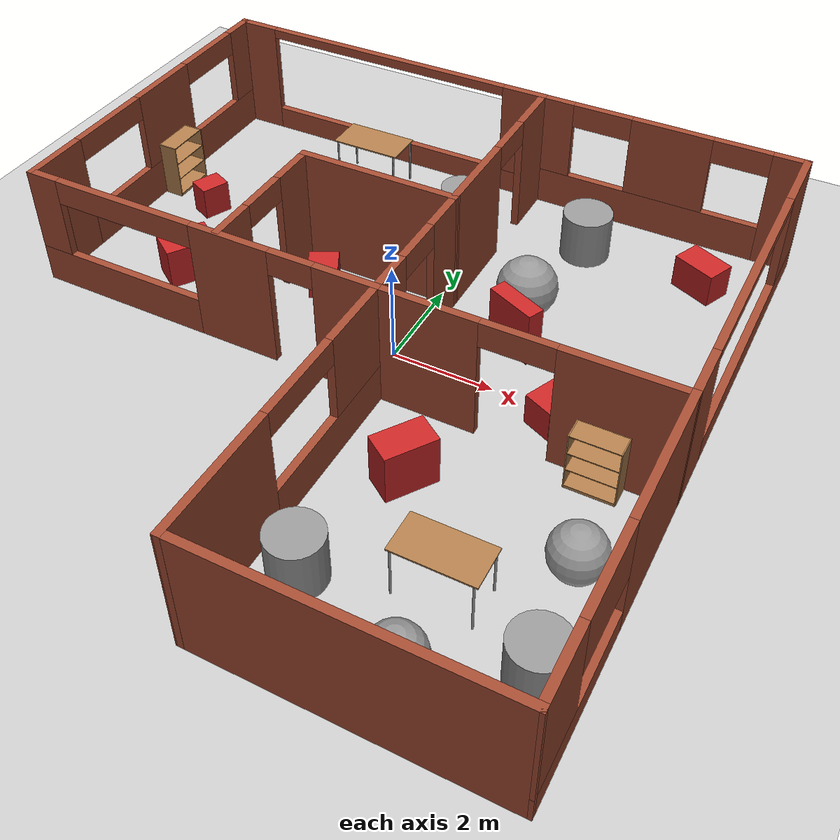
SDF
<sdf version="1.6">
 <world name="default">
  <light name="sun" type="directional">
   <pose>0 0 10 0 -0 0</pose>
   <diffuse>0.8 0.8 0.8 1</diffuse>
   <specular>0.2 0.2 0.2 1</specular>
   <attenuation>
    <range>1000</range>
    <constant>0.9</constant>
    <linear>0.01</linear>
    <quadratic>0.001</quadratic>
   </attenuation>
   <direction>-0.5 0.1 -0.9</direction>
  </light>
  <model name="ground_plane">
   <static>1</static>
   <link name="link">
    <collision name="collision">
     <geometry><plane><normal>0 0 1</normal><size>100 100</size></plane></geometry>
     <surface>
      <contact><collide_bitmask>65535</collide_bitmask></contact>
      <friction><ode><mu>100</mu><mu2>50</mu2></ode></friction>
     </surface>
    </collision>
    <visual name="visual">
     <cast_shadows>0</cast_shadows>
     <geometry><plane><normal>0 0 1</normal><size>100 100</size></plane></geometry>
     <material>
      <script><uri>file://media/materials/scripts/gazebo.material</uri><name>Gazebo/Grey</name></script>
     </material>
    </visual>
   </link>
  </model>
  <gravity>0 0 -9.8</gravity>
  <magnetic_field>6e-06 2.3e-05 -4.2e-05</magnetic_field>
  <atmosphere type="adiabatic"/>
  <physics name="default_physics" default="0" type="ode">
   <max_step_size>0.001</max_step_size>
   <real_time_factor>1</real_time_factor>
   <real_time_update_rate>1000</real_time_update_rate>
  </physics>
  <scene><ambient>0.4 0.4 0.4 1</ambient><background>0.7 0.7 0.7 1</background><shadows>1</shadows></scene>
  <spherical_coordinates>
   <surface_model>EARTH_WGS84</surface_model>
   <latitude_deg>0</latitude_deg>
   <longitude_deg>0</longitude_deg>
   <elevation>0</elevation>
   <heading_deg>0</heading_deg>
  </spherical_coordinates>
  <model name="bookshelf">
   <static>1</static>
   <link name="link">
    <inertial><mass>1</mass></inertial>
    <collision name="back">
     <pose>0 0.005 0.6 0 -0 0</pose>
     <geometry><box><size>0.9 0.01 1.2</size></box></geometry>
    </collision>
    <visual name="visual1">
     <pose>0 0.005 0.6 0 -0 0</pose>
     <geometry><box><size>0.9 0.01 1.2</size></box></geometry>
     <material>
      <script><uri>file://media/materials/scripts/gazebo.material</uri><name>Gazebo/Wood</name></script>
     </material>
    </visual>
    <collision name="left_side">
     <pose>0.45 -0.195 0.6 0 -0 0</pose>
     <geometry><box><size>0.02 0.4 1.2</size></box></geometry>
    </collision>
    <visual name="visual2">
     <pose>0.45 -0.195 0.6 0 -0 0</pose>
     <geometry><box><size>0.02 0.4 1.2</size></box></geometry>
     <material>
      <script><uri>file://media/materials/scripts/gazebo.material</uri><name>Gazebo/Wood</name></script>
     </material>
    </visual>
    <collision name="right_side">
     <pose>-0.45 -0.195 0.6 0 -0 0</pose>
     <geometry><box><size>0.02 0.4 1.2</size></box></geometry>
    </collision>
    <visual name="visual3">
     <pose>-0.45 -0.195 0.6 0 -0 0</pose>
     <geometry><box><size>0.02 0.4 1.2</size></box></geometry>
     <material>
      <script><uri>file://media/materials/scripts/gazebo.material</uri><name>Gazebo/Wood</name></script>
     </material>
    </visual>
    <collision name="bottom">
     <pose>0 -0.195 0.03 0 -0 0</pose>
     <geometry><box><size>0.88 0.4 0.06</size></box></geometry>
    </collision>
    <visual name="visual4">
     <pose>0 -0.195 0.03 0 -0 0</pose>
     <geometry><box><size>0.88 0.4 0.06</size></box></geometry>
     <material>
      <script><uri>file://media/materials/scripts/gazebo.material</uri><name>Gazebo/Wood</name></script>
     </material>
    </visual>
    <collision name="top">
     <pose>0 -0.195 1.19 0 -0 0</pose>
     <geometry><box><size>0.88 0.4 0.02</size></box></geometry>
    </collision>
    <visual name="visual5">
     <pose>0 -0.195 1.19 0 -0 0</pose>
     <geometry><box><size>0.88 0.4 0.02</size></box></geometry>
     <material>
      <script><uri>file://media/materials/scripts/gazebo.material</uri><name>Gazebo/Wood</name></script>
     </material>
    </visual>
    <collision name="low_shelf">
     <pose>0 -0.195 0.43 0 -0 0</pose>
     <geometry><box><size>0.88 0.4 0.02</size></box></geometry>
    </collision>
    <visual name="visual6">
     <pose>0 -0.195 0.43 0 -0 0</pose>
     <geometry><box><size>0.88 0.4 0.02</size></box></geometry>
     <material>
      <script><uri>file://media/materials/scripts/gazebo.material</uri><name>Gazebo/Wood</name></script>
     </material>
    </visual>
    <collision name="high_shelf">
     <pose>0 -0.195 0.8 0 -0 0</pose>
     <geometry><box><size>0.88 0.4 0.02</size></box></geometry>
    </collision>
    <visual name="visual7">
     <pose>0 -0.195 0.8 0 -0 0</pose>
     <geometry><box><size>0.88 0.4 0.02</size></box></geometry>
     <material>
      <script><uri>file://media/materials/scripts/gazebo.material</uri><name>Gazebo/Wood</name></script>
     </material>
    </visual>
   </link>
   <pose>-6.96679 2.8402 0 0 -0 1.5708</pose>
  </model>
  <model name="table">
   <static>1</static>
   <link name="link">
    <collision name="surface">
     <pose>0 0 1 0 -0 0</pose>
     <geometry><box><size>1.5 0.8 0.03</size></box></geometry>
     <surface><friction><ode><mu>0.6</mu><mu2>0.6</mu2></ode></friction></surface>
    </collision>
    <visual name="visual1">
     <pose>0 0 1 0 -0 0</pose>
     <geometry><box><size>1.5 0.8 0.03</size></box></geometry>
     <material>
      <script><uri>file://media/materials/scripts/gazebo.material</uri><name>Gazebo/Wood</name></script>
     </material>
    </visual>
    <collision name="front_left_leg">
     <pose>0.68 0.38 0.5 0 -0 0</pose>
     <geometry><cylinder><radius>0.02</radius><length>1</length></cylinder></geometry>
    </collision>
    <visual name="front_left_leg">
     <pose>0.68 0.38 0.5 0 -0 0</pose>
     <geometry><cylinder><radius>0.02</radius><length>1</length></cylinder></geometry>
     <material>
      <script><uri>file://media/materials/scripts/gazebo.material</uri><name>Gazebo/Grey</name></script>
     </material>
    </visual>
    <collision name="front_right_leg">
     <pose>0.68 -0.38 0.5 0 -0 0</pose>
     <geometry><cylinder><radius>0.02</radius><length>1</length></cylinder></geometry>
    </collision>
    <visual name="front_right_leg">
     <pose>0.68 -0.38 0.5 0 -0 0</pose>
     <geometry><cylinder><radius>0.02</radius><length>1</length></cylinder></geometry>
     <material>
      <script><uri>file://media/materials/scripts/gazebo.material</uri><name>Gazebo/Grey</name></script>
     </material>
    </visual>
    <collision name="back_right_leg">
     <pose>-0.68 -0.38 0.5 0 -0 0</pose>
     <geometry><cylinder><radius>0.02</radius><length>1</length></cylinder></geometry>
    </collision>
    <visual name="back_right_leg">
     <pose>-0.68 -0.38 0.5 0 -0 0</pose>
     <geometry><cylinder><radius>0.02</radius><length>1</length></cylinder></geometry>
     <material>
      <script><uri>file://media/materials/scripts/gazebo.material</uri><name>Gazebo/Grey</name></script>
     </material>
    </visual>
    <collision name="back_left_leg">
     <pose>-0.68 0.38 0.5 0 -0 0</pose>
     <geometry><cylinder><radius>0.02</radius><length>1</length></cylinder></geometry>
    </collision>
    <visual name="back_left_leg">
     <pose>-0.68 0.38 0.5 0 -0 0</pose>
     <geometry><cylinder><radius>0.02</radius><length>1</length></cylinder></geometry>
     <material>
      <script><uri>file://media/materials/scripts/gazebo.material</uri><name>Gazebo/Grey</name></script>
     </material>
    </visual>
   </link>
   <pose>-3.15936 4.91977 0 0 -0 0</pose>
  </model>
  <model name="unit_cylinder">
   <pose>-0.951249 4.77245 0.286507 0 0 -0.507211</pose>
   <link name="link">
    <inertial>
     <mass>1</mass>
     <inertia><ixx>0.145833</ixx><ixy>0</ixy><ixz>0</ixz><iyy>0.145833</iyy><iyz>0</iyz><izz>0.125</izz></inertia>
    </inertial>
    <collision name="collision">
     <geometry><cylinder><radius>0.443131</radius><length>0.573015</length></cylinder></geometry>
    </collision>
    <visual name="visual">
     <geometry><cylinder><radius>0.443131</radius><length>0.573015</length></cylinder></geometry>
     <material>
      <script><name>Gazebo/Grey</name><uri>file://media/materials/scripts/gazebo.material</uri></script>
     </material>
    </visual>
   </link>
  </model>
  <model name="table_clone">
   <static>1</static>
   <link name="link">
    <collision name="surface">
     <pose>0 0 1 0 -0 0</pose>
     <geometry><box><size>1.5 0.8 0.03</size></box></geometry>
     <surface><friction><ode><mu>0.6</mu><mu2>0.6</mu2></ode></friction></surface>
    </collision>
    <visual name="visual1">
     <pose>0 0 1 0 -0 0</pose>
     <geometry><box><size>1.5 0.8 0.03</size></box></geometry>
     <material>
      <script><uri>file://media/materials/scripts/gazebo.material</uri><name>Gazebo/Wood</name></script>
     </material>
    </visual>
    <collision name="front_left_leg">
     <pose>0.68 0.38 0.5 0 -0 0</pose>
     <geometry><cylinder><radius>0.02</radius><length>1</length></cylinder></geometry>
    </collision>
    <visual name="front_left_leg">
     <pose>0.68 0.38 0.5 0 -0 0</pose>
     <geometry><cylinder><radius>0.02</radius><length>1</length></cylinder></geometry>
     <material>
      <script><uri>file://media/materials/scripts/gazebo.material</uri><name>Gazebo/Grey</name></script>
     </material>
    </visual>
    <collision name="front_right_leg">
     <pose>0.68 -0.38 0.5 0 -0 0</pose>
     <geometry><cylinder><radius>0.02</radius><length>1</length></cylinder></geometry>
    </collision>
    <visual name="front_right_leg">
     <pose>0.68 -0.38 0.5 0 -0 0</pose>
     <geometry><cylinder><radius>0.02</radius><length>1</length></cylinder></geometry>
     <material>
      <script><uri>file://media/materials/scripts/gazebo.material</uri><name>Gazebo/Grey</name></script>
     </material>
    </visual>
    <collision name="back_right_leg">
     <pose>-0.68 -0.38 0.5 0 -0 0</pose>
     <geometry><cylinder><radius>0.02</radius><length>1</length></cylinder></geometry>
    </collision>
    <visual name="back_right_leg">
     <pose>-0.68 -0.38 0.5 0 -0 0</pose>
     <geometry><cylinder><radius>0.02</radius><length>1</length></cylinder></geometry>
     <material>
      <script><uri>file://media/materials/scripts/gazebo.material</uri><name>Gazebo/Grey</name></script>
     </material>
    </visual>
    <collision name="back_left_leg">
     <pose>-0.68 0.38 0.5 0 -0 0</pose>
     <geometry><cylinder><radius>0.02</radius><length>1</length></cylinder></geometry>
    </collision>
    <visual name="back_left_leg">
     <pose>-0.68 0.38 0.5 0 -0 0</pose>
     <geometry><cylinder><radius>0.02</radius><length>1</length></cylinder></geometry>
     <material>
      <script><uri>file://media/materials/scripts/gazebo.material</uri><name>Gazebo/Grey</name></script>
     </material>
    </visual>
   </link>
   <pose>3.16978 -4.27284 0 0 -0 0</pose>
  </model>
  <model name="bookshelf_clone">
   <static>1</static>
   <link name="link">
    <inertial><mass>1</mass></inertial>
    <collision name="back">
     <pose>0 0.005 0.6 0 -0 0</pose>
     <geometry><box><size>0.9 0.01 1.2</size></box></geometry>
    </collision>
    <visual name="visual1">
     <pose>0 0.005 0.6 0 -0 0</pose>
     <geometry><box><size>0.9 0.01 1.2</size></box></geometry>
     <material>
      <script><uri>file://media/materials/scripts/gazebo.material</uri><name>Gazebo/Wood</name></script>
     </material>
    </visual>
    <collision name="left_side">
     <pose>0.45 -0.195 0.6 0 -0 0</pose>
     <geometry><box><size>0.02 0.4 1.2</size></box></geometry>
    </collision>
    <visual name="visual2">
     <pose>0.45 -0.195 0.6 0 -0 0</pose>
     <geometry><box><size>0.02 0.4 1.2</size></box></geometry>
     <material>
      <script><uri>file://media/materials/scripts/gazebo.material</uri><name>Gazebo/Wood</name></script>
     </material>
    </visual>
    <collision name="right_side">
     <pose>-0.45 -0.195 0.6 0 -0 0</pose>
     <geometry><box><size>0.02 0.4 1.2</size></box></geometry>
    </collision>
    <visual name="visual3">
     <pose>-0.45 -0.195 0.6 0 -0 0</pose>
     <geometry><box><size>0.02 0.4 1.2</size></box></geometry>
     <material>
      <script><uri>file://media/materials/scripts/gazebo.material</uri><name>Gazebo/Wood</name></script>
     </material>
    </visual>
    <collision name="bottom">
     <pose>0 -0.195 0.03 0 -0 0</pose>
     <geometry><box><size>0.88 0.4 0.06</size></box></geometry>
    </collision>
    <visual name="visual4">
     <pose>0 -0.195 0.03 0 -0 0</pose>
     <geometry><box><size>0.88 0.4 0.06</size></box></geometry>
     <material>
      <script><uri>file://media/materials/scripts/gazebo.material</uri><name>Gazebo/Wood</name></script>
     </material>
    </visual>
    <collision name="top">
     <pose>0 -0.195 1.19 0 -0 0</pose>
     <geometry><box><size>0.88 0.4 0.02</size></box></geometry>
    </collision>
    <visual name="visual5">
     <pose>0 -0.195 1.19 0 -0 0</pose>
     <geometry><box><size>0.88 0.4 0.02</size></box></geometry>
     <material>
      <script><uri>file://media/materials/scripts/gazebo.material</uri><name>Gazebo/Wood</name></script>
     </material>
    </visual>
    <collision name="low_shelf">
     <pose>0 -0.195 0.43 0 -0 0</pose>
     <geometry><box><size>0.88 0.4 0.02</size></box></geometry>
    </collision>
    <visual name="visual6">
     <pose>0 -0.195 0.43 0 -0 0</pose>
     <geometry><box><size>0.88 0.4 0.02</size></box></geometry>
     <material>
      <script><uri>file://media/materials/scripts/gazebo.material</uri><name>Gazebo/Wood</name></script>
     </material>
    </visual>
    <collision name="high_shelf">
     <pose>0 -0.195 0.8 0 -0 0</pose>
     <geometry><box><size>0.88 0.4 0.02</size></box></geometry>
    </collision>
    <visual name="visual7">
     <pose>0 -0.195 0.8 0 -0 0</pose>
     <geometry><box><size>0.88 0.4 0.02</size></box></geometry>
     <material>
      <script><uri>file://media/materials/scripts/gazebo.material</uri><name>Gazebo/Wood</name></script>
     </material>
    </visual>
   </link>
   <pose>4.43049 -1.13981 0 0 -0 4e-06</pose>
  </model>
  <model name="unit_sphere">
   <pose>-3.59754 3.23444 0.5 0 -0 0</pose>
   <link name="link">
    <inertial>
     <mass>1</mass>
     <inertia><ixx>0.1</ixx><ixy>0</ixy><ixz>0</ixz><iyy>0.1</iyy><iyz>0</iyz><izz>0.1</izz></inertia>
    </inertial>
    <collision name="collision"><geometry><sphere><radius>0.5</radius></sphere></geometry></collision>
    <visual name="visual">
     <geometry><sphere><radius>0.5</radius></sphere></geometry>
     <material>
      <script><name>Gazebo/Grey</name><uri>file://media/materials/scripts/gazebo.material</uri></script>
     </material>
    </visual>
   </link>
  </model>
  <model name="unit_cylinder_0">
   <pose>-1.50045 2.96064 0.299235 0 0 -1.03302</pose>
   <link name="link">
    <inertial>
     <mass>1</mass>
     <inertia><ixx>0.145833</ixx><ixy>0</ixy><ixz>0</ixz><iyy>0.145833</iyy><iyz>0</iyz><izz>0.125</izz></inertia>
    </inertial>
    <collision name="collision">
     <geometry><cylinder><radius>0.386388</radius><length>0.59847</length></cylinder></geometry>
    </collision>
    <visual name="visual">
     <geometry><cylinder><radius>0.386388</radius><length>0.59847</length></cylinder></geometry>
     <material>
      <script><name>Gazebo/Grey</name><uri>file://media/materials/scripts/gazebo.material</uri></script>
     </material>
    </visual>
   </link>
  </model>
  <model name="unit_cylinder_1">
   <pose>1.96335 4.55514 0.5 0 -0 0</pose>
   <link name="link">
    <inertial>
     <mass>1</mass>
     <inertia><ixx>0.145833</ixx><ixy>0</ixy><ixz>0</ixz><iyy>0.145833</iyy><iyz>0</iyz><izz>0.125</izz></inertia>
    </inertial>
    <collision name="collision">
     <geometry><cylinder><radius>0.501667</radius><length>1</length></cylinder></geometry>
    </collision>
    <visual name="visual">
     <geometry><cylinder><radius>0.501667</radius><length>1</length></cylinder></geometry>
     <material>
      <script><name>Gazebo/Grey</name><uri>file://media/materials/scripts/gazebo.material</uri></script>
     </material>
    </visual>
   </link>
  </model>
  <model name="unit_sphere_0">
   <pose>1.6417 2.30704 0.591817 0 -0 0</pose>
   <link name="link">
    <inertial>
     <mass>1</mass>
     <inertia><ixx>0.1</ixx><ixy>0</ixy><ixz>0</ixz><iyy>0.1</iyy><iyz>0</iyz><izz>0.1</izz></inertia>
    </inertial>
    <collision name="collision"><geometry><sphere><radius>0.591817</radius></sphere></geometry></collision>
    <visual name="visual">
     <geometry><sphere><radius>0.591817</radius></sphere></geometry>
     <material>
      <script><name>Gazebo/Grey</name><uri>file://media/materials/scripts/gazebo.material</uri></script>
     </material>
    </visual>
   </link>
  </model>
  <model name="unit_sphere_1">
   <pose>4.81114 -3.03675 0.5 0 -0 0</pose>
   <link name="link">
    <inertial>
     <mass>1</mass>
     <inertia><ixx>0.1</ixx><ixy>0</ixy><ixz>0</ixz><iyy>0.1</iyy><iyz>0</iyz><izz>0.1</izz></inertia>
    </inertial>
    <collision name="collision"><geometry><sphere><radius>0.5</radius></sphere></geometry></collision>
    <visual name="visual">
     <geometry><sphere><radius>0.5</radius></sphere></geometry>
     <material>
      <script><name>Gazebo/Grey</name><uri>file://media/materials/scripts/gazebo.material</uri></script>
     </material>
    </visual>
   </link>
  </model>
  <model name="unit_cylinder_2">
   <pose>1.09935 -5.01847 0.5 0 -0 0</pose>
   <link name="link">
    <inertial>
     <mass>1</mass>
     <inertia><ixx>0.145833</ixx><ixy>0</ixy><ixz>0</ixz><iyy>0.145833</iyy><iyz>0</iyz><izz>0.125</izz></inertia>
    </inertial>
    <collision name="collision">
     <geometry><cylinder><radius>0.500001</radius><length>1</length></cylinder></geometry>
    </collision>
    <visual name="visual">
     <geometry><cylinder><radius>0.500001</radius><length>1</length></cylinder></geometry>
     <material>
      <script><name>Gazebo/Grey</name><uri>file://media/materials/scripts/gazebo.material</uri></script>
     </material>
    </visual>
   </link>
  </model>
  <model name="unit_sphere_2">
   <pose>3.22839 -5.83427 0.5 0 -0 0</pose>
   <link name="link">
    <inertial>
     <mass>1</mass>
     <inertia><ixx>0.1</ixx><ixy>0</ixy><ixz>0</ixz><iyy>0.1</iyy><iyz>0</iyz><izz>0.1</izz></inertia>
    </inertial>
    <collision name="collision"><geometry><sphere><radius>0.5</radius></sphere></geometry></collision>
    <visual name="visual">
     <geometry><sphere><radius>0.5</radius></sphere></geometry>
     <material>
      <script><name>Gazebo/Grey</name><uri>file://media/materials/scripts/gazebo.material</uri></script>
     </material>
    </visual>
   </link>
  </model>
  <model name="unit_cylinder_3">
   <pose>5.01945 -5.03504 0.5 0 -0 0</pose>
   <link name="link">
    <inertial>
     <mass>1</mass>
     <inertia><ixx>0.145833</ixx><ixy>0</ixy><ixz>0</ixz><iyy>0.145833</iyy><iyz>0</iyz><izz>0.125</izz></inertia>
    </inertial>
    <collision name="collision">
     <geometry><cylinder><radius>0.5</radius><length>1</length></cylinder></geometry>
    </collision>
    <visual name="visual">
     <geometry><cylinder><radius>0.5</radius><length>1</length></cylinder></geometry>
     <material>
      <script><name>Gazebo/Grey</name><uri>file://media/materials/scripts/gazebo.material</uri></script>
     </material>
    </visual>
   </link>
  </model>
  <model name="AssignmentBuilding_0">
   <link name="Wall_36">
    <pose>-2.70744 6.37584 0 0 -0 0</pose>
    <inertial>
     <mass>1</mass>
     <inertia><ixx>1</ixx><ixy>0</ixy><ixz>0</ixz><iyy>1</iyy><iyz>0</iyz><izz>1</izz></inertia>
    </inertial>
    <visual name="Wall_36_Visual_0">
     <pose>-3.28639 0 1.25 0 -0 0</pose>
     <geometry><box><size>0.927226 0.15 2.5</size></box></geometry>
     <material>
      <script><uri>file://media/materials/scripts/gazebo.material</uri><name>Gazebo/Bricks</name></script>
      <ambient>1 1 1 1</ambient>
      <shader type="pixel"><normal_map>__default__</normal_map></shader>
      <diffuse>0 0 0 1</diffuse>
      <specular>0 0 0 1</specular>
      <emissive>0 0 0 1</emissive>
     </material>
     <meta><layer>0</layer></meta>
    </visual>
    <visual name="Wall_36_Visual_1">
     <pose>0.463613 0 0.25 0 -0 0</pose>
     <geometry><box><size>6.57277 0.15 0.5</size></box></geometry>
     <material>
      <script><uri>file://media/materials/scripts/gazebo.material</uri><name>Gazebo/Bricks</name></script>
      <ambient>1 1 1 1</ambient>
      <shader type="pixel"><normal_map>__default__</normal_map></shader>
      <diffuse>0.7 0.7 0.7 1</diffuse>
      <specular>0.01 0.01 0.01 1</specular>
      <emissive>0 0 0 1</emissive>
     </material>
     <meta><layer>0</layer></meta>
    </visual>
    <visual name="Wall_36_Visual_2">
     <pose>3.27261 0 1.5 0 -0 0</pose>
     <geometry><box><size>0.954774 0.15 2</size></box></geometry>
     <material>
      <script><uri>file://media/materials/scripts/gazebo.material</uri><name>Gazebo/Bricks</name></script>
      <ambient>1 1 1 1</ambient>
      <shader type="pixel"><normal_map>__default__</normal_map></shader>
      <diffuse>0.7 0.7 0.7 1</diffuse>
      <specular>0.01 0.01 0.01 1</specular>
      <emissive>0 0 0 1</emissive>
     </material>
     <meta><layer>0</layer></meta>
    </visual>
    <visual name="Wall_36_Visual_3">
     <pose>-0.013774 0 2.4 0 -0 0</pose>
     <geometry><box><size>5.618 0.15 0.2</size></box></geometry>
     <material>
      <script><uri>file://media/materials/scripts/gazebo.material</uri><name>Gazebo/Bricks</name></script>
      <ambient>1 1 1 1</ambient>
      <shader type="pixel"><normal_map>__default__</normal_map></shader>
      <diffuse>0.7 0.7 0.7 1</diffuse>
      <specular>0.01 0.01 0.01 1</specular>
      <emissive>0 0 0 1</emissive>
     </material>
     <meta><layer>0</layer></meta>
    </visual>
    <collision name="Wall_36_Collision_0">
     <pose>-3.28639 0 1.25 0 -0 0</pose>
     <geometry><box><size>0.927226 0.15 2.5</size></box></geometry>
     <surface>
      <friction>
       <ode><mu>1</mu><mu2>1</mu2><fdir1>0 0 0</fdir1><slip1>0</slip1><slip2>0</slip2></ode>
       <torsional>
        <coefficient>1</coefficient>
        <patch_radius>0</patch_radius>
        <surface_radius>0</surface_radius>
        <use_patch_radius>1</use_patch_radius>
        <ode><slip>0</slip></ode>
       </torsional>
      </friction>
      <bounce><restitution_coefficient>0</restitution_coefficient><threshold>1e+06</threshold></bounce>
      <contact>
       <collide_without_contact>0</collide_without_contact>
       <collide_without_contact_bitmask>1</collide_without_contact_bitmask>
       <collide_bitmask>1</collide_bitmask>
       <ode>
        <soft_cfm>0</soft_cfm>
        <soft_erp>0.2</soft_erp>
        <kp>1e+13</kp>
        <kd>1</kd>
        <max_vel>0.01</max_vel>
        <min_depth>0</min_depth>
       </ode>
       <bullet>
        <split_impulse>1</split_impulse>
        <split_impulse_penetration_threshold>-0.01</split_impulse_penetration_threshold>
        <soft_cfm>0</soft_cfm>
        <soft_erp>0.2</soft_erp>
        <kp>1e+13</kp>
        <kd>1</kd>
       </bullet>
      </contact>
     </surface>
    </collision>
    <collision name="Wall_36_Collision_1">
     <pose>0.463613 0 0.25 0 -0 0</pose>
     <geometry><box><size>6.57277 0.15 0.5</size></box></geometry>
     <surface>
      <friction>
       <ode><mu>1</mu><mu2>1</mu2><fdir1>0 0 0</fdir1><slip1>0</slip1><slip2>0</slip2></ode>
       <torsional>
        <coefficient>1</coefficient>
        <patch_radius>0</patch_radius>
        <surface_radius>0</surface_radius>
        <use_patch_radius>1</use_patch_radius>
        <ode><slip>0</slip></ode>
       </torsional>
      </friction>
      <bounce><restitution_coefficient>0</restitution_coefficient><threshold>1e+06</threshold></bounce>
      <contact>
       <collide_without_contact>0</collide_without_contact>
       <collide_without_contact_bitmask>1</collide_without_contact_bitmask>
       <collide_bitmask>1</collide_bitmask>
       <ode>
        <soft_cfm>0</soft_cfm>
        <soft_erp>0.2</soft_erp>
        <kp>1e+13</kp>
        <kd>1</kd>
        <max_vel>0.01</max_vel>
        <min_depth>0</min_depth>
       </ode>
       <bullet>
        <split_impulse>1</split_impulse>
        <split_impulse_penetration_threshold>-0.01</split_impulse_penetration_threshold>
        <soft_cfm>0</soft_cfm>
        <soft_erp>0.2</soft_erp>
        <kp>1e+13</kp>
        <kd>1</kd>
       </bullet>
      </contact>
     </surface>
    </collision>
    <collision name="Wall_36_Collision_2">
     <pose>3.27261 0 1.5 0 -0 0</pose>
     <geometry><box><size>0.954774 0.15 2</size></box></geometry>
     <surface>
      <friction>
       <ode><mu>1</mu><mu2>1</mu2><fdir1>0 0 0</fdir1><slip1>0</slip1><slip2>0</slip2></ode>
       <torsional>
        <coefficient>1</coefficient>
        <patch_radius>0</patch_radius>
        <surface_radius>0</surface_radius>
        <use_patch_radius>1</use_patch_radius>
        <ode><slip>0</slip></ode>
       </torsional>
      </friction>
      <bounce><restitution_coefficient>0</restitution_coefficient><threshold>1e+06</threshold></bounce>
      <contact>
       <collide_without_contact>0</collide_without_contact>
       <collide_without_contact_bitmask>1</collide_without_contact_bitmask>
       <collide_bitmask>1</collide_bitmask>
       <ode>
        <soft_cfm>0</soft_cfm>
        <soft_erp>0.2</soft_erp>
        <kp>1e+13</kp>
        <kd>1</kd>
        <max_vel>0.01</max_vel>
        <min_depth>0</min_depth>
       </ode>
       <bullet>
        <split_impulse>1</split_impulse>
        <split_impulse_penetration_threshold>-0.01</split_impulse_penetration_threshold>
        <soft_cfm>0</soft_cfm>
        <soft_erp>0.2</soft_erp>
        <kp>1e+13</kp>
        <kd>1</kd>
       </bullet>
      </contact>
     </surface>
    </collision>
    <collision name="Wall_36_Collision_3">
     <pose>-0.013774 0 2.4 0 -0 0</pose>
     <geometry><box><size>5.618 0.15 0.2</size></box></geometry>
     <surface>
      <friction>
       <ode><mu>1</mu><mu2>1</mu2><fdir1>0 0 0</fdir1><slip1>0</slip1><slip2>0</slip2></ode>
       <torsional>
        <coefficient>1</coefficient>
        <patch_radius>0</patch_radius>
        <surface_radius>0</surface_radius>
        <use_patch_radius>1</use_patch_radius>
        <ode><slip>0</slip></ode>
       </torsional>
      </friction>
      <bounce><restitution_coefficient>0</restitution_coefficient><threshold>1e+06</threshold></bounce>
      <contact>
       <collide_without_contact>0</collide_without_contact>
       <collide_without_contact_bitmask>1</collide_without_contact_bitmask>
       <collide_bitmask>1</collide_bitmask>
       <ode>
        <soft_cfm>0</soft_cfm>
        <soft_erp>0.2</soft_erp>
        <kp>1e+13</kp>
        <kd>1</kd>
        <max_vel>0.01</max_vel>
        <min_depth>0</min_depth>
       </ode>
       <bullet>
        <split_impulse>1</split_impulse>
        <split_impulse_penetration_threshold>-0.01</split_impulse_penetration_threshold>
        <soft_cfm>0</soft_cfm>
        <soft_erp>0.2</soft_erp>
        <kp>1e+13</kp>
        <kd>1</kd>
       </bullet>
      </contact>
     </surface>
    </collision>
   </link>
   <link name="Wall_37">
    <pose>0.967555 4.32584 0 0 0 -1.5708</pose>
    <inertial>
     <mass>1</mass>
     <inertia><ixx>1</ixx><ixy>0</ixy><ixz>0</ixz><iyy>1</iyy><iyz>0</iyz><izz>1</izz></inertia>
    </inertial>
    <visual name="Wall_37_Visual_1">
     <pose>1.14152 0 1.25 0 -0 0</pose>
     <geometry><box><size>1.96696 0.15 2.5</size></box></geometry>
     <material>
      <script><uri>file://media/materials/scripts/gazebo.material</uri><name>Gazebo/Bricks</name></script>
      <ambient>1 1 1 1</ambient>
      <shader type="pixel"><normal_map>__default__</normal_map></shader>
      <diffuse>0.7 0.7 0.7 1</diffuse>
      <specular>0.01 0.01 0.01 1</specular>
      <emissive>0 0 0 1</emissive>
     </material>
     <meta><layer>0</layer></meta>
    </visual>
    <visual name="Wall_37_Visual_0">
     <pose>-1.50876 0 1.25 0 -0 0</pose>
     <geometry><box><size>1.23247 0.15 2.5</size></box></geometry>
     <material>
      <script><uri>file://media/materials/scripts/gazebo.material</uri><name>Gazebo/Bricks</name></script>
      <ambient>1 1 1 1</ambient>
      <shader type="pixel"><normal_map>__default__</normal_map></shader>
      <diffuse>0.7 0.7 0.7 1</diffuse>
      <specular>0.01 0.01 0.01 1</specular>
      <emissive>0 0 0 1</emissive>
     </material>
     <meta><layer>0</layer></meta>
    </visual>
    <visual name="Wall_37_Visual_2">
     <pose>-0.367245 0 2.25 0 -0 0</pose>
     <geometry><box><size>1.05057 0.15 0.5</size></box></geometry>
     <material>
      <script><uri>file://media/materials/scripts/gazebo.material</uri><name>Gazebo/Bricks</name></script>
      <ambient>1 1 1 1</ambient>
      <shader type="pixel"><normal_map>__default__</normal_map></shader>
      <diffuse>0.7 0.7 0.7 1</diffuse>
      <specular>0.01 0.01 0.01 1</specular>
      <emissive>0 0 0 1</emissive>
     </material>
     <meta><layer>0</layer></meta>
    </visual>
    <collision name="Wall_37_Collision_0">
     <pose>-1.50876 0 1.25 0 -0 0</pose>
     <geometry><box><size>1.23247 0.15 2.5</size></box></geometry>
     <surface>
      <friction>
       <ode><mu>1</mu><mu2>1</mu2><fdir1>0 0 0</fdir1><slip1>0</slip1><slip2>0</slip2></ode>
       <torsional>
        <coefficient>1</coefficient>
        <patch_radius>0</patch_radius>
        <surface_radius>0</surface_radius>
        <use_patch_radius>1</use_patch_radius>
        <ode><slip>0</slip></ode>
       </torsional>
      </friction>
      <bounce><restitution_coefficient>0</restitution_coefficient><threshold>1e+06</threshold></bounce>
      <contact>
       <collide_without_contact>0</collide_without_contact>
       <collide_without_contact_bitmask>1</collide_without_contact_bitmask>
       <collide_bitmask>1</collide_bitmask>
       <ode>
        <soft_cfm>0</soft_cfm>
        <soft_erp>0.2</soft_erp>
        <kp>1e+13</kp>
        <kd>1</kd>
        <max_vel>0.01</max_vel>
        <min_depth>0</min_depth>
       </ode>
       <bullet>
        <split_impulse>1</split_impulse>
        <split_impulse_penetration_threshold>-0.01</split_impulse_penetration_threshold>
        <soft_cfm>0</soft_cfm>
        <soft_erp>0.2</soft_erp>
        <kp>1e+13</kp>
        <kd>1</kd>
       </bullet>
      </contact>
     </surface>
    </collision>
    <collision name="Wall_37_Collision_1">
     <pose>1.14152 0 1.25 0 -0 0</pose>
     <geometry><box><size>1.96696 0.15 2.5</size></box></geometry>
     <surface>
      <friction>
       <ode><mu>1</mu><mu2>1</mu2><fdir1>0 0 0</fdir1><slip1>0</slip1><slip2>0</slip2></ode>
       <torsional>
        <coefficient>1</coefficient>
        <patch_radius>0</patch_radius>
        <surface_radius>0</surface_radius>
        <use_patch_radius>1</use_patch_radius>
        <ode><slip>0</slip></ode>
       </torsional>
      </friction>
      <bounce><restitution_coefficient>0</restitution_coefficient><threshold>1e+06</threshold></bounce>
      <contact>
       <collide_without_contact>0</collide_without_contact>
       <collide_without_contact_bitmask>1</collide_without_contact_bitmask>
       <collide_bitmask>1</collide_bitmask>
       <ode>
        <soft_cfm>0</soft_cfm>
        <soft_erp>0.2</soft_erp>
        <kp>1e+13</kp>
        <kd>1</kd>
        <max_vel>0.01</max_vel>
        <min_depth>0</min_depth>
       </ode>
       <bullet>
        <split_impulse>1</split_impulse>
        <split_impulse_penetration_threshold>-0.01</split_impulse_penetration_threshold>
        <soft_cfm>0</soft_cfm>
        <soft_erp>0.2</soft_erp>
        <kp>1e+13</kp>
        <kd>1</kd>
       </bullet>
      </contact>
     </surface>
    </collision>
    <collision name="Wall_37_Collision_2">
     <pose>-0.367245 0 2.25 0 -0 0</pose>
     <geometry><box><size>1.05057 0.15 0.5</size></box></geometry>
     <surface>
      <friction>
       <ode><mu>1</mu><mu2>1</mu2><fdir1>0 0 0</fdir1><slip1>0</slip1><slip2>0</slip2></ode>
       <torsional>
        <coefficient>1</coefficient>
        <patch_radius>0</patch_radius>
        <surface_radius>0</surface_radius>
        <use_patch_radius>1</use_patch_radius>
        <ode><slip>0</slip></ode>
       </torsional>
      </friction>
      <bounce><restitution_coefficient>0</restitution_coefficient><threshold>1e+06</threshold></bounce>
      <contact>
       <collide_without_contact>0</collide_without_contact>
       <collide_without_contact_bitmask>1</collide_without_contact_bitmask>
       <collide_bitmask>1</collide_bitmask>
       <ode>
        <soft_cfm>0</soft_cfm>
        <soft_erp>0.2</soft_erp>
        <kp>1e+13</kp>
        <kd>1</kd>
        <max_vel>0.01</max_vel>
        <min_depth>0</min_depth>
       </ode>
       <bullet>
        <split_impulse>1</split_impulse>
        <split_impulse_penetration_threshold>-0.01</split_impulse_penetration_threshold>
        <soft_cfm>0</soft_cfm>
        <soft_erp>0.2</soft_erp>
        <kp>1e+13</kp>
        <kd>1</kd>
       </bullet>
      </contact>
     </surface>
    </collision>
   </link>
   <link name="Wall_40">
    <pose>3.66768 6.37584 0 0 0 -3.14159</pose>
    <inertial>
     <mass>1</mass>
     <inertia><ixx>1</ixx><ixy>0</ixy><ixz>0</ixz><iyy>1</iyy><iyz>0</iyz><izz>1</izz></inertia>
    </inertial>
    <visual name="Wall_40_Visual_0">
     <pose>-2.41668 0 1.25 0 -0 0</pose>
     <geometry><box><size>0.71689 0.15 2.5</size></box></geometry>
     <material>
      <script><uri>file://media/materials/scripts/gazebo.material</uri><name>Gazebo/Bricks</name></script>
      <ambient>1 1 1 1</ambient>
      <shader type="pixel"><normal_map>__default__</normal_map></shader>
      <diffuse>1 1 1 1</diffuse>
      <specular>0.2 0.2 0.2 1</specular>
      <emissive>0 0 0 1</emissive>
     </material>
     <meta><layer>0</layer></meta>
    </visual>
    <visual name="Wall_40_Visual_1">
     <pose>0.358445 0 0.4 0 -0 0</pose>
     <geometry><box><size>4.83337 0.15 0.8</size></box></geometry>
     <material>
      <script><uri>file://media/materials/scripts/gazebo.material</uri><name>Gazebo/Bricks</name></script>
      <ambient>1 1 1 1</ambient>
      <shader type="pixel"><normal_map>__default__</normal_map></shader>
      <diffuse>0.7 0.7 0.7 1</diffuse>
      <specular>0.01 0.01 0.01 1</specular>
      <emissive>0 0 0 1</emissive>
     </material>
     <meta><layer>0</layer></meta>
    </visual>
    <visual name="Wall_40_Visual_2">
     <pose>-0.0658 0 1.65 0 -0 0</pose>
     <geometry><box><size>1.66352 0.15 1.7</size></box></geometry>
     <material>
      <script><uri>file://media/materials/scripts/gazebo.material</uri><name>Gazebo/Bricks</name></script>
      <ambient>1 1 1 1</ambient>
      <shader type="pixel"><normal_map>__default__</normal_map></shader>
      <diffuse>0.7 0.7 0.7 1</diffuse>
      <specular>0.01 0.01 0.01 1</specular>
      <emissive>0 0 0 1</emissive>
     </material>
     <meta><layer>0</layer></meta>
    </visual>
    <visual name="Wall_40_Visual_3">
     <pose>2.38491 0 1.65 0 -0 0</pose>
     <geometry><box><size>0.780436 0.15 1.7</size></box></geometry>
     <material>
      <script><uri>file://media/materials/scripts/gazebo.material</uri><name>Gazebo/Bricks</name></script>
      <ambient>1 1 1 1</ambient>
      <shader type="pixel"><normal_map>__default__</normal_map></shader>
      <diffuse>0.7 0.7 0.7 1</diffuse>
      <specular>0.01 0.01 0.01 1</specular>
      <emissive>0 0 0 1</emissive>
     </material>
     <meta><layer>0</layer></meta>
    </visual>
    <visual name="Wall_40_Visual_4">
     <pose>-1.4779 0 2.25 0 -0 0</pose>
     <geometry><box><size>1.16068 0.15 0.5</size></box></geometry>
     <material>
      <script><uri>file://media/materials/scripts/gazebo.material</uri><name>Gazebo/Bricks</name></script>
      <ambient>1 1 1 1</ambient>
      <shader type="pixel"><normal_map>__default__</normal_map></shader>
      <diffuse>0.7 0.7 0.7 1</diffuse>
      <specular>0.01 0.01 0.01 1</specular>
      <emissive>0 0 0 1</emissive>
     </material>
     <meta><layer>0</layer></meta>
    </visual>
    <visual name="Wall_40_Visual_5">
     <pose>1.38033 0 2.25 0 -0 0</pose>
     <geometry><box><size>1.22873 0.15 0.5</size></box></geometry>
     <material>
      <script><uri>file://media/materials/scripts/gazebo.material</uri><name>Gazebo/Bricks</name></script>
      <ambient>1 1 1 1</ambient>
      <shader type="pixel"><normal_map>__default__</normal_map></shader>
      <diffuse>0.7 0.7 0.7 1</diffuse>
      <specular>0.01 0.01 0.01 1</specular>
      <emissive>0 0 0 1</emissive>
     </material>
     <meta><layer>0</layer></meta>
    </visual>
    <collision name="Wall_40_Collision_0">
     <pose>-2.41668 0 1.25 0 -0 0</pose>
     <geometry><box><size>0.71689 0.15 2.5</size></box></geometry>
     <surface>
      <friction>
       <ode><mu>1</mu><mu2>1</mu2><fdir1>0 0 0</fdir1><slip1>0</slip1><slip2>0</slip2></ode>
       <torsional>
        <coefficient>1</coefficient>
        <patch_radius>0</patch_radius>
        <surface_radius>0</surface_radius>
        <use_patch_radius>1</use_patch_radius>
        <ode><slip>0</slip></ode>
       </torsional>
      </friction>
      <bounce><restitution_coefficient>0</restitution_coefficient><threshold>1e+06</threshold></bounce>
      <contact>
       <collide_without_contact>0</collide_without_contact>
       <collide_without_contact_bitmask>1</collide_without_contact_bitmask>
       <collide_bitmask>1</collide_bitmask>
       <ode>
        <soft_cfm>0</soft_cfm>
        <soft_erp>0.2</soft_erp>
        <kp>1e+13</kp>
        <kd>1</kd>
        <max_vel>0.01</max_vel>
        <min_depth>0</min_depth>
       </ode>
       <bullet>
        <split_impulse>1</split_impulse>
        <split_impulse_penetration_threshold>-0.01</split_impulse_penetration_threshold>
        <soft_cfm>0</soft_cfm>
        <soft_erp>0.2</soft_erp>
        <kp>1e+13</kp>
        <kd>1</kd>
       </bullet>
      </contact>
     </surface>
    </collision>
    <collision name="Wall_40_Collision_1">
     <pose>0.358445 0 0.4 0 -0 0</pose>
     <geometry><box><size>4.83337 0.15 0.8</size></box></geometry>
     <surface>
      <friction>
       <ode><mu>1</mu><mu2>1</mu2><fdir1>0 0 0</fdir1><slip1>0</slip1><slip2>0</slip2></ode>
       <torsional>
        <coefficient>1</coefficient>
        <patch_radius>0</patch_radius>
        <surface_radius>0</surface_radius>
        <use_patch_radius>1</use_patch_radius>
        <ode><slip>0</slip></ode>
       </torsional>
      </friction>
      <bounce><restitution_coefficient>0</restitution_coefficient><threshold>1e+06</threshold></bounce>
      <contact>
       <collide_without_contact>0</collide_without_contact>
       <collide_without_contact_bitmask>1</collide_without_contact_bitmask>
       <collide_bitmask>1</collide_bitmask>
       <ode>
        <soft_cfm>0</soft_cfm>
        <soft_erp>0.2</soft_erp>
        <kp>1e+13</kp>
        <kd>1</kd>
        <max_vel>0.01</max_vel>
        <min_depth>0</min_depth>
       </ode>
       <bullet>
        <split_impulse>1</split_impulse>
        <split_impulse_penetration_threshold>-0.01</split_impulse_penetration_threshold>
        <soft_cfm>0</soft_cfm>
        <soft_erp>0.2</soft_erp>
        <kp>1e+13</kp>
        <kd>1</kd>
       </bullet>
      </contact>
     </surface>
    </collision>
    <collision name="Wall_40_Collision_2">
     <pose>-0.0658 0 1.65 0 -0 0</pose>
     <geometry><box><size>1.66352 0.15 1.7</size></box></geometry>
     <surface>
      <friction>
       <ode><mu>1</mu><mu2>1</mu2><fdir1>0 0 0</fdir1><slip1>0</slip1><slip2>0</slip2></ode>
       <torsional>
        <coefficient>1</coefficient>
        <patch_radius>0</patch_radius>
        <surface_radius>0</surface_radius>
        <use_patch_radius>1</use_patch_radius>
        <ode><slip>0</slip></ode>
       </torsional>
      </friction>
      <bounce><restitution_coefficient>0</restitution_coefficient><threshold>1e+06</threshold></bounce>
      <contact>
       <collide_without_contact>0</collide_without_contact>
       <collide_without_contact_bitmask>1</collide_without_contact_bitmask>
       <collide_bitmask>1</collide_bitmask>
       <ode>
        <soft_cfm>0</soft_cfm>
        <soft_erp>0.2</soft_erp>
        <kp>1e+13</kp>
        <kd>1</kd>
        <max_vel>0.01</max_vel>
        <min_depth>0</min_depth>
       </ode>
       <bullet>
        <split_impulse>1</split_impulse>
        <split_impulse_penetration_threshold>-0.01</split_impulse_penetration_threshold>
        <soft_cfm>0</soft_cfm>
        <soft_erp>0.2</soft_erp>
        <kp>1e+13</kp>
        <kd>1</kd>
       </bullet>
      </contact>
     </surface>
    </collision>
    <collision name="Wall_40_Collision_3">
     <pose>2.38491 0 1.65 0 -0 0</pose>
     <geometry><box><size>0.780436 0.15 1.7</size></box></geometry>
     <surface>
      <friction>
       <ode><mu>1</mu><mu2>1</mu2><fdir1>0 0 0</fdir1><slip1>0</slip1><slip2>0</slip2></ode>
       <torsional>
        <coefficient>1</coefficient>
        <patch_radius>0</patch_radius>
        <surface_radius>0</surface_radius>
        <use_patch_radius>1</use_patch_radius>
        <ode><slip>0</slip></ode>
       </torsional>
      </friction>
      <bounce><restitution_coefficient>0</restitution_coefficient><threshold>1e+06</threshold></bounce>
      <contact>
       <collide_without_contact>0</collide_without_contact>
       <collide_without_contact_bitmask>1</collide_without_contact_bitmask>
       <collide_bitmask>1</collide_bitmask>
       <ode>
        <soft_cfm>0</soft_cfm>
        <soft_erp>0.2</soft_erp>
        <kp>1e+13</kp>
        <kd>1</kd>
        <max_vel>0.01</max_vel>
        <min_depth>0</min_depth>
       </ode>
       <bullet>
        <split_impulse>1</split_impulse>
        <split_impulse_penetration_threshold>-0.01</split_impulse_penetration_threshold>
        <soft_cfm>0</soft_cfm>
        <soft_erp>0.2</soft_erp>
        <kp>1e+13</kp>
        <kd>1</kd>
       </bullet>
      </contact>
     </surface>
    </collision>
    <collision name="Wall_40_Collision_4">
     <pose>-1.4779 0 2.25 0 -0 0</pose>
     <geometry><box><size>1.16068 0.15 0.5</size></box></geometry>
     <surface>
      <friction>
       <ode><mu>1</mu><mu2>1</mu2><fdir1>0 0 0</fdir1><slip1>0</slip1><slip2>0</slip2></ode>
       <torsional>
        <coefficient>1</coefficient>
        <patch_radius>0</patch_radius>
        <surface_radius>0</surface_radius>
        <use_patch_radius>1</use_patch_radius>
        <ode><slip>0</slip></ode>
       </torsional>
      </friction>
      <bounce><restitution_coefficient>0</restitution_coefficient><threshold>1e+06</threshold></bounce>
      <contact>
       <collide_without_contact>0</collide_without_contact>
       <collide_without_contact_bitmask>1</collide_without_contact_bitmask>
       <collide_bitmask>1</collide_bitmask>
       <ode>
        <soft_cfm>0</soft_cfm>
        <soft_erp>0.2</soft_erp>
        <kp>1e+13</kp>
        <kd>1</kd>
        <max_vel>0.01</max_vel>
        <min_depth>0</min_depth>
       </ode>
       <bullet>
        <split_impulse>1</split_impulse>
        <split_impulse_penetration_threshold>-0.01</split_impulse_penetration_threshold>
        <soft_cfm>0</soft_cfm>
        <soft_erp>0.2</soft_erp>
        <kp>1e+13</kp>
        <kd>1</kd>
       </bullet>
      </contact>
     </surface>
    </collision>
    <collision name="Wall_40_Collision_5">
     <pose>1.38033 0 2.25 0 -0 0</pose>
     <geometry><box><size>1.22873 0.15 0.5</size></box></geometry>
     <surface>
      <friction>
       <ode><mu>1</mu><mu2>1</mu2><fdir1>0 0 0</fdir1><slip1>0</slip1><slip2>0</slip2></ode>
       <torsional>
        <coefficient>1</coefficient>
        <patch_radius>0</patch_radius>
        <surface_radius>0</surface_radius>
        <use_patch_radius>1</use_patch_radius>
        <ode><slip>0</slip></ode>
       </torsional>
      </friction>
      <bounce><restitution_coefficient>0</restitution_coefficient><threshold>1e+06</threshold></bounce>
      <contact>
       <collide_without_contact>0</collide_without_contact>
       <collide_without_contact_bitmask>1</collide_without_contact_bitmask>
       <collide_bitmask>1</collide_bitmask>
       <ode>
        <soft_cfm>0</soft_cfm>
        <soft_erp>0.2</soft_erp>
        <kp>1e+13</kp>
        <kd>1</kd>
        <max_vel>0.01</max_vel>
        <min_depth>0</min_depth>
       </ode>
       <bullet>
        <split_impulse>1</split_impulse>
        <split_impulse_penetration_threshold>-0.01</split_impulse_penetration_threshold>
        <soft_cfm>0</soft_cfm>
        <soft_erp>0.2</soft_erp>
        <kp>1e+13</kp>
        <kd>1</kd>
       </bullet>
      </contact>
     </surface>
    </collision>
   </link>
   <link name="Wall_42">
    <pose>-0.631247 2.27475 0 0 -0 0.000678</pose>
    <inertial>
     <mass>1</mass>
     <inertia><ixx>1</ixx><ixy>0</ixy><ixz>0</ixz><iyy>1</iyy><iyz>0</iyz><izz>1</izz></inertia>
    </inertial>
    <visual name="Wall_42_Visual">
     <pose>0 0 1.25 0 -0 0</pose>
     <geometry><box><size>3.34761 0.15 2.5</size></box></geometry>
     <material>
      <script><uri>file://media/materials/scripts/gazebo.material</uri><name>Gazebo/Bricks</name></script>
      <ambient>1 1 1 1</ambient>
      <shader type="pixel"><normal_map>__default__</normal_map></shader>
      <diffuse>1 1 1 1</diffuse>
      <specular>0.2 0.2 0.2 1</specular>
      <emissive>0 0 0 1</emissive>
     </material>
     <meta><layer>0</layer></meta>
    </visual>
    <collision name="Wall_42_Collision">
     <pose>0 0 1.25 0 -0 0</pose>
     <geometry><box><size>3.34761 0.15 2.5</size></box></geometry>
     <surface>
      <friction>
       <ode><mu>1</mu><mu2>1</mu2><fdir1>0 0 0</fdir1><slip1>0</slip1><slip2>0</slip2></ode>
       <torsional>
        <coefficient>1</coefficient>
        <patch_radius>0</patch_radius>
        <surface_radius>0</surface_radius>
        <use_patch_radius>1</use_patch_radius>
        <ode><slip>0</slip></ode>
       </torsional>
      </friction>
      <bounce><restitution_coefficient>0</restitution_coefficient><threshold>1e+06</threshold></bounce>
      <contact>
       <collide_without_contact>0</collide_without_contact>
       <collide_without_contact_bitmask>1</collide_without_contact_bitmask>
       <collide_bitmask>1</collide_bitmask>
       <ode>
        <soft_cfm>0</soft_cfm>
        <soft_erp>0.2</soft_erp>
        <kp>1e+13</kp>
        <kd>1</kd>
        <max_vel>0.01</max_vel>
        <min_depth>0</min_depth>
       </ode>
       <bullet>
        <split_impulse>1</split_impulse>
        <split_impulse_penetration_threshold>-0.01</split_impulse_penetration_threshold>
        <soft_cfm>0</soft_cfm>
        <soft_erp>0.2</soft_erp>
        <kp>1e+13</kp>
        <kd>1</kd>
       </bullet>
      </contact>
     </surface>
    </collision>
   </link>
   <link name="Wall_44">
    <pose>0.967092 0.829751 0 0 -0 1.57048</pose>
    <inertial>
     <mass>1</mass>
     <inertia><ixx>1</ixx><ixy>0</ixy><ixz>0</ixz><iyy>1</iyy><iyz>0</iyz><izz>1</izz></inertia>
    </inertial>
    <visual name="Wall_44_Visual_1">
     <pose>1.00948 0 1.25 0 -0 0</pose>
     <geometry><box><size>1.02321 0.15 2.5</size></box></geometry>
     <material>
      <script><uri>file://media/materials/scripts/gazebo.material</uri><name>Gazebo/Bricks</name></script>
      <ambient>1 1 1 1</ambient>
      <shader type="pixel"><normal_map>__default__</normal_map></shader>
      <diffuse>0.7 0.7 0.7 1</diffuse>
      <specular>0.01 0.01 0.01 1</specular>
      <emissive>0 0 0 1</emissive>
     </material>
     <meta><layer>0</layer></meta>
    </visual>
    <visual name="Wall_44_Visual_0">
     <pose>-1.03005 0 1.25 0 -0 0</pose>
     <geometry><box><size>0.982074 0.15 2.5</size></box></geometry>
     <material>
      <script><uri>file://media/materials/scripts/gazebo.material</uri><name>Gazebo/Bricks</name></script>
      <ambient>1 1 1 1</ambient>
      <shader type="pixel"><normal_map>__default__</normal_map></shader>
      <diffuse>1 1 1 1</diffuse>
      <specular>0.2 0.2 0.2 1</specular>
      <emissive>0 0 0 1</emissive>
     </material>
     <meta><layer>0</layer></meta>
    </visual>
    <visual name="Wall_44_Visual_2">
     <pose>-0.020568 0 2.25 0 -0 0</pose>
     <geometry><box><size>1.03689 0.15 0.5</size></box></geometry>
     <material>
      <script><uri>file://media/materials/scripts/gazebo.material</uri><name>Gazebo/Bricks</name></script>
      <ambient>1 1 1 1</ambient>
      <shader type="pixel"><normal_map>__default__</normal_map></shader>
      <diffuse>0.7 0.7 0.7 1</diffuse>
      <specular>0.01 0.01 0.01 1</specular>
      <emissive>0 0 0 1</emissive>
     </material>
     <meta><layer>0</layer></meta>
    </visual>
    <collision name="Wall_44_Collision_0">
     <pose>-1.03005 0 1.25 0 -0 0</pose>
     <geometry><box><size>0.982074 0.15 2.5</size></box></geometry>
     <surface>
      <friction>
       <ode><mu>1</mu><mu2>1</mu2><fdir1>0 0 0</fdir1><slip1>0</slip1><slip2>0</slip2></ode>
       <torsional>
        <coefficient>1</coefficient>
        <patch_radius>0</patch_radius>
        <surface_radius>0</surface_radius>
        <use_patch_radius>1</use_patch_radius>
        <ode><slip>0</slip></ode>
       </torsional>
      </friction>
      <bounce><restitution_coefficient>0</restitution_coefficient><threshold>1e+06</threshold></bounce>
      <contact>
       <collide_without_contact>0</collide_without_contact>
       <collide_without_contact_bitmask>1</collide_without_contact_bitmask>
       <collide_bitmask>1</collide_bitmask>
       <ode>
        <soft_cfm>0</soft_cfm>
        <soft_erp>0.2</soft_erp>
        <kp>1e+13</kp>
        <kd>1</kd>
        <max_vel>0.01</max_vel>
        <min_depth>0</min_depth>
       </ode>
       <bullet>
        <split_impulse>1</split_impulse>
        <split_impulse_penetration_threshold>-0.01</split_impulse_penetration_threshold>
        <soft_cfm>0</soft_cfm>
        <soft_erp>0.2</soft_erp>
        <kp>1e+13</kp>
        <kd>1</kd>
       </bullet>
      </contact>
     </surface>
    </collision>
    <collision name="Wall_44_Collision_1">
     <pose>1.00948 0 1.25 0 -0 0</pose>
     <geometry><box><size>1.02321 0.15 2.5</size></box></geometry>
     <surface>
      <friction>
       <ode><mu>1</mu><mu2>1</mu2><fdir1>0 0 0</fdir1><slip1>0</slip1><slip2>0</slip2></ode>
       <torsional>
        <coefficient>1</coefficient>
        <patch_radius>0</patch_radius>
        <surface_radius>0</surface_radius>
        <use_patch_radius>1</use_patch_radius>
        <ode><slip>0</slip></ode>
       </torsional>
      </friction>
      <bounce><restitution_coefficient>0</restitution_coefficient><threshold>1e+06</threshold></bounce>
      <contact>
       <collide_without_contact>0</collide_without_contact>
       <collide_without_contact_bitmask>1</collide_without_contact_bitmask>
       <collide_bitmask>1</collide_bitmask>
       <ode>
        <soft_cfm>0</soft_cfm>
        <soft_erp>0.2</soft_erp>
        <kp>1e+13</kp>
        <kd>1</kd>
        <max_vel>0.01</max_vel>
        <min_depth>0</min_depth>
       </ode>
       <bullet>
        <split_impulse>1</split_impulse>
        <split_impulse_penetration_threshold>-0.01</split_impulse_penetration_threshold>
        <soft_cfm>0</soft_cfm>
        <soft_erp>0.2</soft_erp>
        <kp>1e+13</kp>
        <kd>1</kd>
       </bullet>
      </contact>
     </surface>
    </collision>
    <collision name="Wall_44_Collision_2">
     <pose>-0.020568 0 2.25 0 -0 0</pose>
     <geometry><box><size>1.03689 0.15 0.5</size></box></geometry>
     <surface>
      <friction>
       <ode><mu>1</mu><mu2>1</mu2><fdir1>0 0 0</fdir1><slip1>0</slip1><slip2>0</slip2></ode>
       <torsional>
        <coefficient>1</coefficient>
        <patch_radius>0</patch_radius>
        <surface_radius>0</surface_radius>
        <use_patch_radius>1</use_patch_radius>
        <ode><slip>0</slip></ode>
       </torsional>
      </friction>
      <bounce><restitution_coefficient>0</restitution_coefficient><threshold>1e+06</threshold></bounce>
      <contact>
       <collide_without_contact>0</collide_without_contact>
       <collide_without_contact_bitmask>1</collide_without_contact_bitmask>
       <collide_bitmask>1</collide_bitmask>
       <ode>
        <soft_cfm>0</soft_cfm>
        <soft_erp>0.2</soft_erp>
        <kp>1e+13</kp>
        <kd>1</kd>
        <max_vel>0.01</max_vel>
        <min_depth>0</min_depth>
       </ode>
       <bullet>
        <split_impulse>1</split_impulse>
        <split_impulse_penetration_threshold>-0.01</split_impulse_penetration_threshold>
        <soft_cfm>0</soft_cfm>
        <soft_erp>0.2</soft_erp>
        <kp>1e+13</kp>
        <kd>1</kd>
       </bullet>
      </contact>
     </surface>
    </collision>
   </link>
   <link name="Wall_46">
    <pose>6.37502 2.87945 0 0 -0 1.57286</pose>
    <inertial>
     <mass>1</mass>
     <inertia><ixx>1</ixx><ixy>0</ixy><ixz>0</ixz><iyy>1</iyy><iyz>0</iyz><izz>1</izz></inertia>
    </inertial>
    <visual name="Wall_46_Visual_0">
     <pose>-2.99489 0 1.25 0 -0 0</pose>
     <geometry><box><size>1.15301 0.15 2.5</size></box></geometry>
     <material>
      <script><uri>file://media/materials/scripts/gazebo.material</uri><name>Gazebo/Bricks</name></script>
      <ambient>1 1 1 1</ambient>
      <shader type="pixel"><normal_map>__default__</normal_map></shader>
      <diffuse>1 1 1 1</diffuse>
      <specular>0.2 0.2 0.2 1</specular>
      <emissive>0 0 0 1</emissive>
     </material>
     <meta><layer>0</layer></meta>
    </visual>
    <visual name="Wall_46_Visual_1">
     <pose>0.576503 0 0.2495 0 -0 0</pose>
     <geometry><box><size>5.98978 0.15 0.499</size></box></geometry>
     <material>
      <script><uri>file://media/materials/scripts/gazebo.material</uri><name>Gazebo/Bricks</name></script>
      <ambient>1 1 1 1</ambient>
      <shader type="pixel"><normal_map>__default__</normal_map></shader>
      <diffuse>0.7 0.7 0.7 1</diffuse>
      <specular>0.01 0.01 0.01 1</specular>
      <emissive>0 0 0 1</emissive>
     </material>
     <meta><layer>0</layer></meta>
    </visual>
    <visual name="Wall_46_Visual_2">
     <pose>2.865 0 1.4995 0 -0 0</pose>
     <geometry><box><size>1.41278 0.15 2.001</size></box></geometry>
     <material>
      <script><uri>file://media/materials/scripts/gazebo.material</uri><name>Gazebo/Bricks</name></script>
      <ambient>1 1 1 1</ambient>
      <shader type="pixel"><normal_map>__default__</normal_map></shader>
      <diffuse>0.7 0.7 0.7 1</diffuse>
      <specular>0.01 0.01 0.01 1</specular>
      <emissive>0 0 0 1</emissive>
     </material>
     <meta><layer>0</layer></meta>
    </visual>
    <visual name="Wall_46_Visual_3">
     <pose>-0.129889 0 2.3995 0 -0 0</pose>
     <geometry><box><size>4.577 0.15 0.201</size></box></geometry>
     <material>
      <script><uri>file://media/materials/scripts/gazebo.material</uri><name>Gazebo/Bricks</name></script>
      <ambient>1 1 1 1</ambient>
      <shader type="pixel"><normal_map>__default__</normal_map></shader>
      <diffuse>0.7 0.7 0.7 1</diffuse>
      <specular>0.01 0.01 0.01 1</specular>
      <emissive>0 0 0 1</emissive>
     </material>
     <meta><layer>0</layer></meta>
    </visual>
    <collision name="Wall_46_Collision_0">
     <pose>-2.99489 0 1.25 0 -0 0</pose>
     <geometry><box><size>1.15301 0.15 2.5</size></box></geometry>
     <surface>
      <friction>
       <ode><mu>1</mu><mu2>1</mu2><fdir1>0 0 0</fdir1><slip1>0</slip1><slip2>0</slip2></ode>
       <torsional>
        <coefficient>1</coefficient>
        <patch_radius>0</patch_radius>
        <surface_radius>0</surface_radius>
        <use_patch_radius>1</use_patch_radius>
        <ode><slip>0</slip></ode>
       </torsional>
      </friction>
      <bounce><restitution_coefficient>0</restitution_coefficient><threshold>1e+06</threshold></bounce>
      <contact>
       <collide_without_contact>0</collide_without_contact>
       <collide_without_contact_bitmask>1</collide_without_contact_bitmask>
       <collide_bitmask>1</collide_bitmask>
       <ode>
        <soft_cfm>0</soft_cfm>
        <soft_erp>0.2</soft_erp>
        <kp>1e+13</kp>
        <kd>1</kd>
        <max_vel>0.01</max_vel>
        <min_depth>0</min_depth>
       </ode>
       <bullet>
        <split_impulse>1</split_impulse>
        <split_impulse_penetration_threshold>-0.01</split_impulse_penetration_threshold>
        <soft_cfm>0</soft_cfm>
        <soft_erp>0.2</soft_erp>
        <kp>1e+13</kp>
        <kd>1</kd>
       </bullet>
      </contact>
     </surface>
    </collision>
    <collision name="Wall_46_Collision_1">
     <pose>0.576503 0 0.2495 0 -0 0</pose>
     <geometry><box><size>5.98978 0.15 0.499</size></box></geometry>
     <surface>
      <friction>
       <ode><mu>1</mu><mu2>1</mu2><fdir1>0 0 0</fdir1><slip1>0</slip1><slip2>0</slip2></ode>
       <torsional>
        <coefficient>1</coefficient>
        <patch_radius>0</patch_radius>
        <surface_radius>0</surface_radius>
        <use_patch_radius>1</use_patch_radius>
        <ode><slip>0</slip></ode>
       </torsional>
      </friction>
      <bounce><restitution_coefficient>0</restitution_coefficient><threshold>1e+06</threshold></bounce>
      <contact>
       <collide_without_contact>0</collide_without_contact>
       <collide_without_contact_bitmask>1</collide_without_contact_bitmask>
       <collide_bitmask>1</collide_bitmask>
       <ode>
        <soft_cfm>0</soft_cfm>
        <soft_erp>0.2</soft_erp>
        <kp>1e+13</kp>
        <kd>1</kd>
        <max_vel>0.01</max_vel>
        <min_depth>0</min_depth>
       </ode>
       <bullet>
        <split_impulse>1</split_impulse>
        <split_impulse_penetration_threshold>-0.01</split_impulse_penetration_threshold>
        <soft_cfm>0</soft_cfm>
        <soft_erp>0.2</soft_erp>
        <kp>1e+13</kp>
        <kd>1</kd>
       </bullet>
      </contact>
     </surface>
    </collision>
    <collision name="Wall_46_Collision_2">
     <pose>2.865 0 1.4995 0 -0 0</pose>
     <geometry><box><size>1.41278 0.15 2.001</size></box></geometry>
     <surface>
      <friction>
       <ode><mu>1</mu><mu2>1</mu2><fdir1>0 0 0</fdir1><slip1>0</slip1><slip2>0</slip2></ode>
       <torsional>
        <coefficient>1</coefficient>
        <patch_radius>0</patch_radius>
        <surface_radius>0</surface_radius>
        <use_patch_radius>1</use_patch_radius>
        <ode><slip>0</slip></ode>
       </torsional>
      </friction>
      <bounce><restitution_coefficient>0</restitution_coefficient><threshold>1e+06</threshold></bounce>
      <contact>
       <collide_without_contact>0</collide_without_contact>
       <collide_without_contact_bitmask>1</collide_without_contact_bitmask>
       <collide_bitmask>1</collide_bitmask>
       <ode>
        <soft_cfm>0</soft_cfm>
        <soft_erp>0.2</soft_erp>
        <kp>1e+13</kp>
        <kd>1</kd>
        <max_vel>0.01</max_vel>
        <min_depth>0</min_depth>
       </ode>
       <bullet>
        <split_impulse>1</split_impulse>
        <split_impulse_penetration_threshold>-0.01</split_impulse_penetration_threshold>
        <soft_cfm>0</soft_cfm>
        <soft_erp>0.2</soft_erp>
        <kp>1e+13</kp>
        <kd>1</kd>
       </bullet>
      </contact>
     </surface>
    </collision>
    <collision name="Wall_46_Collision_3">
     <pose>-0.129889 0 2.3995 0 -0 0</pose>
     <geometry><box><size>4.577 0.15 0.201</size></box></geometry>
     <surface>
      <friction>
       <ode><mu>1</mu><mu2>1</mu2><fdir1>0 0 0</fdir1><slip1>0</slip1><slip2>0</slip2></ode>
       <torsional>
        <coefficient>1</coefficient>
        <patch_radius>0</patch_radius>
        <surface_radius>0</surface_radius>
        <use_patch_radius>1</use_patch_radius>
        <ode><slip>0</slip></ode>
       </torsional>
      </friction>
      <bounce><restitution_coefficient>0</restitution_coefficient><threshold>1e+06</threshold></bounce>
      <contact>
       <collide_without_contact>0</collide_without_contact>
       <collide_without_contact_bitmask>1</collide_without_contact_bitmask>
       <collide_bitmask>1</collide_bitmask>
       <ode>
        <soft_cfm>0</soft_cfm>
        <soft_erp>0.2</soft_erp>
        <kp>1e+13</kp>
        <kd>1</kd>
        <max_vel>0.01</max_vel>
        <min_depth>0</min_depth>
       </ode>
       <bullet>
        <split_impulse>1</split_impulse>
        <split_impulse_penetration_threshold>-0.01</split_impulse_penetration_threshold>
        <soft_cfm>0</soft_cfm>
        <soft_erp>0.2</soft_erp>
        <kp>1e+13</kp>
        <kd>1</kd>
       </bullet>
      </contact>
     </surface>
    </collision>
   </link>
   <link name="Wall_48">
    <pose>-6.38208 2.87945 0 0 -0 1.5709</pose>
    <inertial>
     <mass>1</mass>
     <inertia><ixx>1</ixx><ixy>0</ixy><ixz>0</ixz><iyy>1</iyy><iyz>0</iyz><izz>1</izz></inertia>
    </inertial>
    <visual name="Wall_48_Visual_0">
     <pose>-2.89905 0 1.25 0 -0 0</pose>
     <geometry><box><size>1.34467 0.15 2.5</size></box></geometry>
     <material>
      <script><uri>file://media/materials/scripts/gazebo.material</uri><name>Gazebo/Bricks</name></script>
      <ambient>1 1 1 1</ambient>
      <shader type="pixel"><normal_map>__default__</normal_map></shader>
      <diffuse>1 1 1 1</diffuse>
      <specular>0.2 0.2 0.2 1</specular>
      <emissive>0 0 0 1</emissive>
     </material>
     <meta><layer>0</layer></meta>
    </visual>
    <visual name="Wall_48_Visual_1">
     <pose>0.672335 0 0.4 0 -0 0</pose>
     <geometry><box><size>5.7981 0.15 0.8</size></box></geometry>
     <material>
      <script><uri>file://media/materials/scripts/gazebo.material</uri><name>Gazebo/Bricks</name></script>
      <ambient>1 1 1 1</ambient>
      <shader type="pixel"><normal_map>__default__</normal_map></shader>
      <diffuse>0.7 0.7 0.7 1</diffuse>
      <specular>0.01 0.01 0.01 1</specular>
      <emissive>0 0 0 1</emissive>
     </material>
     <meta><layer>0</layer></meta>
    </visual>
    <visual name="Wall_48_Visual_2">
     <pose>0.391018 0 1.65 0 -0 0</pose>
     <geometry><box><size>1.60972 0.15 1.7</size></box></geometry>
     <material>
      <script><uri>file://media/materials/scripts/gazebo.material</uri><name>Gazebo/Bricks</name></script>
      <ambient>1 1 1 1</ambient>
      <shader type="pixel"><normal_map>__default__</normal_map></shader>
      <diffuse>0.7 0.7 0.7 1</diffuse>
      <specular>0.01 0.01 0.01 1</specular>
      <emissive>0 0 0 1</emissive>
     </material>
     <meta><layer>0</layer></meta>
    </visual>
    <visual name="Wall_48_Visual_3">
     <pose>3.19363 0 1.65 0 -0 0</pose>
     <geometry><box><size>0.755509 0.15 1.7</size></box></geometry>
     <material>
      <script><uri>file://media/materials/scripts/gazebo.material</uri><name>Gazebo/Bricks</name></script>
      <ambient>1 1 1 1</ambient>
      <shader type="pixel"><normal_map>__default__</normal_map></shader>
      <diffuse>0.7 0.7 0.7 1</diffuse>
      <specular>0.01 0.01 0.01 1</specular>
      <emissive>0 0 0 1</emissive>
     </material>
     <meta><layer>0</layer></meta>
    </visual>
    <visual name="Wall_48_Visual_4">
     <pose>-1.32028 0 2.25 0 -0 0</pose>
     <geometry><box><size>1.81288 0.15 0.5</size></box></geometry>
     <material>
      <script><uri>file://media/materials/scripts/gazebo.material</uri><name>Gazebo/Bricks</name></script>
      <ambient>1 1 1 1</ambient>
      <shader type="pixel"><normal_map>__default__</normal_map></shader>
      <diffuse>0.7 0.7 0.7 1</diffuse>
      <specular>0.01 0.01 0.01 1</specular>
      <emissive>0 0 0 1</emissive>
     </material>
     <meta><layer>0</layer></meta>
    </visual>
    <visual name="Wall_48_Visual_5">
     <pose>2.00588 0 2.25 0 -0 0</pose>
     <geometry><box><size>1.62 0.15 0.5</size></box></geometry>
     <material>
      <script><uri>file://media/materials/scripts/gazebo.material</uri><name>Gazebo/Bricks</name></script>
      <ambient>1 1 1 1</ambient>
      <shader type="pixel"><normal_map>__default__</normal_map></shader>
      <diffuse>0.7 0.7 0.7 1</diffuse>
      <specular>0.01 0.01 0.01 1</specular>
      <emissive>0 0 0 1</emissive>
     </material>
     <meta><layer>0</layer></meta>
    </visual>
    <collision name="Wall_48_Collision_0">
     <pose>-2.89905 0 1.25 0 -0 0</pose>
     <geometry><box><size>1.34467 0.15 2.5</size></box></geometry>
     <surface>
      <friction>
       <ode><mu>1</mu><mu2>1</mu2><fdir1>0 0 0</fdir1><slip1>0</slip1><slip2>0</slip2></ode>
       <torsional>
        <coefficient>1</coefficient>
        <patch_radius>0</patch_radius>
        <surface_radius>0</surface_radius>
        <use_patch_radius>1</use_patch_radius>
        <ode><slip>0</slip></ode>
       </torsional>
      </friction>
      <bounce><restitution_coefficient>0</restitution_coefficient><threshold>1e+06</threshold></bounce>
      <contact>
       <collide_without_contact>0</collide_without_contact>
       <collide_without_contact_bitmask>1</collide_without_contact_bitmask>
       <collide_bitmask>1</collide_bitmask>
       <ode>
        <soft_cfm>0</soft_cfm>
        <soft_erp>0.2</soft_erp>
        <kp>1e+13</kp>
        <kd>1</kd>
        <max_vel>0.01</max_vel>
        <min_depth>0</min_depth>
       </ode>
       <bullet>
        <split_impulse>1</split_impulse>
        <split_impulse_penetration_threshold>-0.01</split_impulse_penetration_threshold>
        <soft_cfm>0</soft_cfm>
        <soft_erp>0.2</soft_erp>
        <kp>1e+13</kp>
        <kd>1</kd>
       </bullet>
      </contact>
     </surface>
    </collision>
    <collision name="Wall_48_Collision_1">
     <pose>0.672335 0 0.4 0 -0 0</pose>
     <geometry><box><size>5.7981 0.15 0.8</size></box></geometry>
     <surface>
      <friction>
       <ode><mu>1</mu><mu2>1</mu2><fdir1>0 0 0</fdir1><slip1>0</slip1><slip2>0</slip2></ode>
       <torsional>
        <coefficient>1</coefficient>
        <patch_radius>0</patch_radius>
        <surface_radius>0</surface_radius>
        <use_patch_radius>1</use_patch_radius>
        <ode><slip>0</slip></ode>
       </torsional>
      </friction>
      <bounce><restitution_coefficient>0</restitution_coefficient><threshold>1e+06</threshold></bounce>
      <contact>
       <collide_without_contact>0</collide_without_contact>
       <collide_without_contact_bitmask>1</collide_without_contact_bitmask>
       <collide_bitmask>1</collide_bitmask>
       <ode>
        <soft_cfm>0</soft_cfm>
        <soft_erp>0.2</soft_erp>
        <kp>1e+13</kp>
        <kd>1</kd>
        <max_vel>0.01</max_vel>
        <min_depth>0</min_depth>
       </ode>
       <bullet>
        <split_impulse>1</split_impulse>
        <split_impulse_penetration_threshold>-0.01</split_impulse_penetration_threshold>
        <soft_cfm>0</soft_cfm>
        <soft_erp>0.2</soft_erp>
        <kp>1e+13</kp>
        <kd>1</kd>
       </bullet>
      </contact>
     </surface>
    </collision>
    <collision name="Wall_48_Collision_2">
     <pose>0.391018 0 1.65 0 -0 0</pose>
     <geometry><box><size>1.60972 0.15 1.7</size></box></geometry>
     <surface>
      <friction>
       <ode><mu>1</mu><mu2>1</mu2><fdir1>0 0 0</fdir1><slip1>0</slip1><slip2>0</slip2></ode>
       <torsional>
        <coefficient>1</coefficient>
        <patch_radius>0</patch_radius>
        <surface_radius>0</surface_radius>
        <use_patch_radius>1</use_patch_radius>
        <ode><slip>0</slip></ode>
       </torsional>
      </friction>
      <bounce><restitution_coefficient>0</restitution_coefficient><threshold>1e+06</threshold></bounce>
      <contact>
       <collide_without_contact>0</collide_without_contact>
       <collide_without_contact_bitmask>1</collide_without_contact_bitmask>
       <collide_bitmask>1</collide_bitmask>
       <ode>
        <soft_cfm>0</soft_cfm>
        <soft_erp>0.2</soft_erp>
        <kp>1e+13</kp>
        <kd>1</kd>
        <max_vel>0.01</max_vel>
        <min_depth>0</min_depth>
       </ode>
       <bullet>
        <split_impulse>1</split_impulse>
        <split_impulse_penetration_threshold>-0.01</split_impulse_penetration_threshold>
        <soft_cfm>0</soft_cfm>
        <soft_erp>0.2</soft_erp>
        <kp>1e+13</kp>
        <kd>1</kd>
       </bullet>
      </contact>
     </surface>
    </collision>
    <collision name="Wall_48_Collision_3">
     <pose>3.19363 0 1.65 0 -0 0</pose>
     <geometry><box><size>0.755509 0.15 1.7</size></box></geometry>
     <surface>
      <friction>
       <ode><mu>1</mu><mu2>1</mu2><fdir1>0 0 0</fdir1><slip1>0</slip1><slip2>0</slip2></ode>
       <torsional>
        <coefficient>1</coefficient>
        <patch_radius>0</patch_radius>
        <surface_radius>0</surface_radius>
        <use_patch_radius>1</use_patch_radius>
        <ode><slip>0</slip></ode>
       </torsional>
      </friction>
      <bounce><restitution_coefficient>0</restitution_coefficient><threshold>1e+06</threshold></bounce>
      <contact>
       <collide_without_contact>0</collide_without_contact>
       <collide_without_contact_bitmask>1</collide_without_contact_bitmask>
       <collide_bitmask>1</collide_bitmask>
       <ode>
        <soft_cfm>0</soft_cfm>
        <soft_erp>0.2</soft_erp>
        <kp>1e+13</kp>
        <kd>1</kd>
        <max_vel>0.01</max_vel>
        <min_depth>0</min_depth>
       </ode>
       <bullet>
        <split_impulse>1</split_impulse>
        <split_impulse_penetration_threshold>-0.01</split_impulse_penetration_threshold>
        <soft_cfm>0</soft_cfm>
        <soft_erp>0.2</soft_erp>
        <kp>1e+13</kp>
        <kd>1</kd>
       </bullet>
      </contact>
     </surface>
    </collision>
    <collision name="Wall_48_Collision_4">
     <pose>-1.32028 0 2.25 0 -0 0</pose>
     <geometry><box><size>1.81288 0.15 0.5</size></box></geometry>
     <surface>
      <friction>
       <ode><mu>1</mu><mu2>1</mu2><fdir1>0 0 0</fdir1><slip1>0</slip1><slip2>0</slip2></ode>
       <torsional>
        <coefficient>1</coefficient>
        <patch_radius>0</patch_radius>
        <surface_radius>0</surface_radius>
        <use_patch_radius>1</use_patch_radius>
        <ode><slip>0</slip></ode>
       </torsional>
      </friction>
      <bounce><restitution_coefficient>0</restitution_coefficient><threshold>1e+06</threshold></bounce>
      <contact>
       <collide_without_contact>0</collide_without_contact>
       <collide_without_contact_bitmask>1</collide_without_contact_bitmask>
       <collide_bitmask>1</collide_bitmask>
       <ode>
        <soft_cfm>0</soft_cfm>
        <soft_erp>0.2</soft_erp>
        <kp>1e+13</kp>
        <kd>1</kd>
        <max_vel>0.01</max_vel>
        <min_depth>0</min_depth>
       </ode>
       <bullet>
        <split_impulse>1</split_impulse>
        <split_impulse_penetration_threshold>-0.01</split_impulse_penetration_threshold>
        <soft_cfm>0</soft_cfm>
        <soft_erp>0.2</soft_erp>
        <kp>1e+13</kp>
        <kd>1</kd>
       </bullet>
      </contact>
     </surface>
    </collision>
    <collision name="Wall_48_Collision_5">
     <pose>2.00588 0 2.25 0 -0 0</pose>
     <geometry><box><size>1.62 0.15 0.5</size></box></geometry>
     <surface>
      <friction>
       <ode><mu>1</mu><mu2>1</mu2><fdir1>0 0 0</fdir1><slip1>0</slip1><slip2>0</slip2></ode>
       <torsional>
        <coefficient>1</coefficient>
        <patch_radius>0</patch_radius>
        <surface_radius>0</surface_radius>
        <use_patch_radius>1</use_patch_radius>
        <ode><slip>0</slip></ode>
       </torsional>
      </friction>
      <bounce><restitution_coefficient>0</restitution_coefficient><threshold>1e+06</threshold></bounce>
      <contact>
       <collide_without_contact>0</collide_without_contact>
       <collide_without_contact_bitmask>1</collide_without_contact_bitmask>
       <collide_bitmask>1</collide_bitmask>
       <ode>
        <soft_cfm>0</soft_cfm>
        <soft_erp>0.2</soft_erp>
        <kp>1e+13</kp>
        <kd>1</kd>
        <max_vel>0.01</max_vel>
        <min_depth>0</min_depth>
       </ode>
       <bullet>
        <split_impulse>1</split_impulse>
        <split_impulse_penetration_threshold>-0.01</split_impulse_penetration_threshold>
        <soft_cfm>0</soft_cfm>
        <soft_erp>0.2</soft_erp>
        <kp>1e+13</kp>
        <kd>1</kd>
       </bullet>
      </contact>
     </surface>
    </collision>
   </link>
   <link name="Wall_50">
    <pose>-2.70755 -0.616637 0 0 0 -3.14151</pose>
    <inertial>
     <mass>1</mass>
     <inertia><ixx>1</ixx><ixy>0</ixy><ixz>0</ixz><iyy>1</iyy><iyz>0</iyz><izz>1</izz></inertia>
    </inertial>
    <visual name="Wall_50_Visual_0">
     <pose>-3.10542 0 1.25 0 -0 0</pose>
     <geometry><box><size>1.28752 0.15 2.5</size></box></geometry>
     <material>
      <script><uri>file://media/materials/scripts/gazebo.material</uri><name>Gazebo/Bricks</name></script>
      <ambient>1 1 1 1</ambient>
      <shader type="pixel"><normal_map>__default__</normal_map></shader>
      <diffuse>1 1 1 1</diffuse>
      <specular>0.2 0.2 0.2 1</specular>
      <emissive>0 0 0 1</emissive>
     </material>
     <meta><layer>0</layer></meta>
    </visual>
    <visual name="Wall_50_Visual_1">
     <pose>-0.739689 0 1.25 0 -0 0</pose>
     <geometry><box><size>1.64394 0.15 2.5</size></box></geometry>
     <material>
      <script><uri>file://media/materials/scripts/gazebo.material</uri><name>Gazebo/Bricks</name></script>
      <ambient>1 1 1 1</ambient>
      <shader type="pixel"><normal_map>__default__</normal_map></shader>
      <diffuse>0.7 0.7 0.7 1</diffuse>
      <specular>0.01 0.01 0.01 1</specular>
      <emissive>0 0 0 1</emissive>
     </material>
     <meta><layer>0</layer></meta>
    </visual>
    <visual name="Wall_50_Visual_2">
     <pose>1.91573 0 0.4 0 -0 0</pose>
     <geometry><box><size>3.6669 0.15 0.8</size></box></geometry>
     <material>
      <script><uri>file://media/materials/scripts/gazebo.material</uri><name>Gazebo/Bricks</name></script>
      <ambient>1 1 1 1</ambient>
      <shader type="pixel"><normal_map>__default__</normal_map></shader>
      <diffuse>0.7 0.7 0.7 1</diffuse>
      <specular>0.01 0.01 0.01 1</specular>
      <emissive>0 0 0 1</emissive>
     </material>
     <meta><layer>0</layer></meta>
    </visual>
    <visual name="Wall_50_Visual_3">
     <pose>3.40754 0 1.65 0 -0 0</pose>
     <geometry><box><size>0.683277 0.15 1.7</size></box></geometry>
     <material>
      <script><uri>file://media/materials/scripts/gazebo.material</uri><name>Gazebo/Bricks</name></script>
      <ambient>1 1 1 1</ambient>
      <shader type="pixel"><normal_map>__default__</normal_map></shader>
      <diffuse>0.7 0.7 0.7 1</diffuse>
      <specular>0.01 0.01 0.01 1</specular>
      <emissive>0 0 0 1</emissive>
     </material>
     <meta><layer>0</layer></meta>
    </visual>
    <visual name="Wall_50_Visual_4">
     <pose>-2.01166 0 2.25 0 -0 0</pose>
     <geometry><box><size>0.9 0.15 0.5</size></box></geometry>
     <material>
      <script><uri>file://media/materials/scripts/gazebo.material</uri><name>Gazebo/Bricks</name></script>
      <ambient>1 1 1 1</ambient>
      <shader type="pixel"><normal_map>__default__</normal_map></shader>
      <diffuse>0.7 0.7 0.7 1</diffuse>
      <specular>0.01 0.01 0.01 1</specular>
      <emissive>0 0 0 1</emissive>
     </material>
     <meta><layer>0</layer></meta>
    </visual>
    <visual name="Wall_50_Visual_5">
     <pose>1.57409 0 2.25 0 -0 0</pose>
     <geometry><box><size>2.98362 0.15 0.5</size></box></geometry>
     <material>
      <script><uri>file://media/materials/scripts/gazebo.material</uri><name>Gazebo/Bricks</name></script>
      <ambient>1 1 1 1</ambient>
      <shader type="pixel"><normal_map>__default__</normal_map></shader>
      <diffuse>0.7 0.7 0.7 1</diffuse>
      <specular>0.01 0.01 0.01 1</specular>
      <emissive>0 0 0 1</emissive>
     </material>
     <meta><layer>0</layer></meta>
    </visual>
    <collision name="Wall_50_Collision_0">
     <pose>-3.10542 0 1.25 0 -0 0</pose>
     <geometry><box><size>1.28752 0.15 2.5</size></box></geometry>
     <surface>
      <friction>
       <ode><mu>1</mu><mu2>1</mu2><fdir1>0 0 0</fdir1><slip1>0</slip1><slip2>0</slip2></ode>
       <torsional>
        <coefficient>1</coefficient>
        <patch_radius>0</patch_radius>
        <surface_radius>0</surface_radius>
        <use_patch_radius>1</use_patch_radius>
        <ode><slip>0</slip></ode>
       </torsional>
      </friction>
      <bounce><restitution_coefficient>0</restitution_coefficient><threshold>1e+06</threshold></bounce>
      <contact>
       <collide_without_contact>0</collide_without_contact>
       <collide_without_contact_bitmask>1</collide_without_contact_bitmask>
       <collide_bitmask>1</collide_bitmask>
       <ode>
        <soft_cfm>0</soft_cfm>
        <soft_erp>0.2</soft_erp>
        <kp>1e+13</kp>
        <kd>1</kd>
        <max_vel>0.01</max_vel>
        <min_depth>0</min_depth>
       </ode>
       <bullet>
        <split_impulse>1</split_impulse>
        <split_impulse_penetration_threshold>-0.01</split_impulse_penetration_threshold>
        <soft_cfm>0</soft_cfm>
        <soft_erp>0.2</soft_erp>
        <kp>1e+13</kp>
        <kd>1</kd>
       </bullet>
      </contact>
     </surface>
    </collision>
    <collision name="Wall_50_Collision_1">
     <pose>-0.739689 0 1.25 0 -0 0</pose>
     <geometry><box><size>1.64394 0.15 2.5</size></box></geometry>
     <surface>
      <friction>
       <ode><mu>1</mu><mu2>1</mu2><fdir1>0 0 0</fdir1><slip1>0</slip1><slip2>0</slip2></ode>
       <torsional>
        <coefficient>1</coefficient>
        <patch_radius>0</patch_radius>
        <surface_radius>0</surface_radius>
        <use_patch_radius>1</use_patch_radius>
        <ode><slip>0</slip></ode>
       </torsional>
      </friction>
      <bounce><restitution_coefficient>0</restitution_coefficient><threshold>1e+06</threshold></bounce>
      <contact>
       <collide_without_contact>0</collide_without_contact>
       <collide_without_contact_bitmask>1</collide_without_contact_bitmask>
       <collide_bitmask>1</collide_bitmask>
       <ode>
        <soft_cfm>0</soft_cfm>
        <soft_erp>0.2</soft_erp>
        <kp>1e+13</kp>
        <kd>1</kd>
        <max_vel>0.01</max_vel>
        <min_depth>0</min_depth>
       </ode>
       <bullet>
        <split_impulse>1</split_impulse>
        <split_impulse_penetration_threshold>-0.01</split_impulse_penetration_threshold>
        <soft_cfm>0</soft_cfm>
        <soft_erp>0.2</soft_erp>
        <kp>1e+13</kp>
        <kd>1</kd>
       </bullet>
      </contact>
     </surface>
    </collision>
    <collision name="Wall_50_Collision_2">
     <pose>1.91573 0 0.4 0 -0 0</pose>
     <geometry><box><size>3.6669 0.15 0.8</size></box></geometry>
     <surface>
      <friction>
       <ode><mu>1</mu><mu2>1</mu2><fdir1>0 0 0</fdir1><slip1>0</slip1><slip2>0</slip2></ode>
       <torsional>
        <coefficient>1</coefficient>
        <patch_radius>0</patch_radius>
        <surface_radius>0</surface_radius>
        <use_patch_radius>1</use_patch_radius>
        <ode><slip>0</slip></ode>
       </torsional>
      </friction>
      <bounce><restitution_coefficient>0</restitution_coefficient><threshold>1e+06</threshold></bounce>
      <contact>
       <collide_without_contact>0</collide_without_contact>
       <collide_without_contact_bitmask>1</collide_without_contact_bitmask>
       <collide_bitmask>1</collide_bitmask>
       <ode>
        <soft_cfm>0</soft_cfm>
        <soft_erp>0.2</soft_erp>
        <kp>1e+13</kp>
        <kd>1</kd>
        <max_vel>0.01</max_vel>
        <min_depth>0</min_depth>
       </ode>
       <bullet>
        <split_impulse>1</split_impulse>
        <split_impulse_penetration_threshold>-0.01</split_impulse_penetration_threshold>
        <soft_cfm>0</soft_cfm>
        <soft_erp>0.2</soft_erp>
        <kp>1e+13</kp>
        <kd>1</kd>
       </bullet>
      </contact>
     </surface>
    </collision>
    <collision name="Wall_50_Collision_3">
     <pose>3.40754 0 1.65 0 -0 0</pose>
     <geometry><box><size>0.683277 0.15 1.7</size></box></geometry>
     <surface>
      <friction>
       <ode><mu>1</mu><mu2>1</mu2><fdir1>0 0 0</fdir1><slip1>0</slip1><slip2>0</slip2></ode>
       <torsional>
        <coefficient>1</coefficient>
        <patch_radius>0</patch_radius>
        <surface_radius>0</surface_radius>
        <use_patch_radius>1</use_patch_radius>
        <ode><slip>0</slip></ode>
       </torsional>
      </friction>
      <bounce><restitution_coefficient>0</restitution_coefficient><threshold>1e+06</threshold></bounce>
      <contact>
       <collide_without_contact>0</collide_without_contact>
       <collide_without_contact_bitmask>1</collide_without_contact_bitmask>
       <collide_bitmask>1</collide_bitmask>
       <ode>
        <soft_cfm>0</soft_cfm>
        <soft_erp>0.2</soft_erp>
        <kp>1e+13</kp>
        <kd>1</kd>
        <max_vel>0.01</max_vel>
        <min_depth>0</min_depth>
       </ode>
       <bullet>
        <split_impulse>1</split_impulse>
        <split_impulse_penetration_threshold>-0.01</split_impulse_penetration_threshold>
        <soft_cfm>0</soft_cfm>
        <soft_erp>0.2</soft_erp>
        <kp>1e+13</kp>
        <kd>1</kd>
       </bullet>
      </contact>
     </surface>
    </collision>
    <collision name="Wall_50_Collision_4">
     <pose>-2.01166 0 2.25 0 -0 0</pose>
     <geometry><box><size>0.9 0.15 0.5</size></box></geometry>
     <surface>
      <friction>
       <ode><mu>1</mu><mu2>1</mu2><fdir1>0 0 0</fdir1><slip1>0</slip1><slip2>0</slip2></ode>
       <torsional>
        <coefficient>1</coefficient>
        <patch_radius>0</patch_radius>
        <surface_radius>0</surface_radius>
        <use_patch_radius>1</use_patch_radius>
        <ode><slip>0</slip></ode>
       </torsional>
      </friction>
      <bounce><restitution_coefficient>0</restitution_coefficient><threshold>1e+06</threshold></bounce>
      <contact>
       <collide_without_contact>0</collide_without_contact>
       <collide_without_contact_bitmask>1</collide_without_contact_bitmask>
       <collide_bitmask>1</collide_bitmask>
       <ode>
        <soft_cfm>0</soft_cfm>
        <soft_erp>0.2</soft_erp>
        <kp>1e+13</kp>
        <kd>1</kd>
        <max_vel>0.01</max_vel>
        <min_depth>0</min_depth>
       </ode>
       <bullet>
        <split_impulse>1</split_impulse>
        <split_impulse_penetration_threshold>-0.01</split_impulse_penetration_threshold>
        <soft_cfm>0</soft_cfm>
        <soft_erp>0.2</soft_erp>
        <kp>1e+13</kp>
        <kd>1</kd>
       </bullet>
      </contact>
     </surface>
    </collision>
    <collision name="Wall_50_Collision_5">
     <pose>1.57409 0 2.25 0 -0 0</pose>
     <geometry><box><size>2.98362 0.15 0.5</size></box></geometry>
     <surface>
      <friction>
       <ode><mu>1</mu><mu2>1</mu2><fdir1>0 0 0</fdir1><slip1>0</slip1><slip2>0</slip2></ode>
       <torsional>
        <coefficient>1</coefficient>
        <patch_radius>0</patch_radius>
        <surface_radius>0</surface_radius>
        <use_patch_radius>1</use_patch_radius>
        <ode><slip>0</slip></ode>
       </torsional>
      </friction>
      <bounce><restitution_coefficient>0</restitution_coefficient><threshold>1e+06</threshold></bounce>
      <contact>
       <collide_without_contact>0</collide_without_contact>
       <collide_without_contact_bitmask>1</collide_without_contact_bitmask>
       <collide_bitmask>1</collide_bitmask>
       <ode>
        <soft_cfm>0</soft_cfm>
        <soft_erp>0.2</soft_erp>
        <kp>1e+13</kp>
        <kd>1</kd>
        <max_vel>0.01</max_vel>
        <min_depth>0</min_depth>
       </ode>
       <bullet>
        <split_impulse>1</split_impulse>
        <split_impulse_penetration_threshold>-0.01</split_impulse_penetration_threshold>
        <soft_cfm>0</soft_cfm>
        <soft_erp>0.2</soft_erp>
        <kp>1e+13</kp>
        <kd>1</kd>
       </bullet>
      </contact>
     </surface>
    </collision>
   </link>
   <link name="Wall_52">
    <pose>0.961018 -3.49604 0 0 -0 1.56885</pose>
    <inertial>
     <mass>1</mass>
     <inertia><ixx>1</ixx><ixy>0</ixy><ixz>0</ixz><iyy>1</iyy><iyz>0</iyz><izz>1</izz></inertia>
    </inertial>
    <visual name="Wall_52_Visual_0">
     <pose>-1.68236 0 1.25 0 -0 0</pose>
     <geometry><box><size>2.5449 0.15 2.5</size></box></geometry>
     <material>
      <script><uri>file://media/materials/scripts/gazebo.material</uri><name>Gazebo/Bricks</name></script>
      <ambient>1 1 1 1</ambient>
      <shader type="pixel"><normal_map>__default__</normal_map></shader>
      <diffuse>1 1 1 1</diffuse>
      <specular>0.2 0.2 0.2 1</specular>
      <emissive>0 0 0 1</emissive>
     </material>
     <meta><layer>0</layer></meta>
    </visual>
    <visual name="Wall_52_Visual_1">
     <pose>1.27245 0 0.4 0 -0 0</pose>
     <geometry><box><size>3.36472 0.15 0.8</size></box></geometry>
     <material>
      <script><uri>file://media/materials/scripts/gazebo.material</uri><name>Gazebo/Bricks</name></script>
      <ambient>1 1 1 1</ambient>
      <shader type="pixel"><normal_map>__default__</normal_map></shader>
      <diffuse>0.7 0.7 0.7 1</diffuse>
      <specular>0.01 0.01 0.01 1</specular>
      <emissive>0 0 0 1</emissive>
     </material>
     <meta><layer>0</layer></meta>
    </visual>
    <visual name="Wall_52_Visual_2">
     <pose>2.17235 0 1.65 0 -0 0</pose>
     <geometry><box><size>1.56492 0.15 1.7</size></box></geometry>
     <material>
      <script><uri>file://media/materials/scripts/gazebo.material</uri><name>Gazebo/Bricks</name></script>
      <ambient>1 1 1 1</ambient>
      <shader type="pixel"><normal_map>__default__</normal_map></shader>
      <diffuse>0.7 0.7 0.7 1</diffuse>
      <specular>0.01 0.01 0.01 1</specular>
      <emissive>0 0 0 1</emissive>
     </material>
     <meta><layer>0</layer></meta>
    </visual>
    <visual name="Wall_52_Visual_3">
     <pose>0.489991 0 2.25 0 -0 0</pose>
     <geometry><box><size>1.79981 0.15 0.5</size></box></geometry>
     <material>
      <script><uri>file://media/materials/scripts/gazebo.material</uri><name>Gazebo/Bricks</name></script>
      <ambient>1 1 1 1</ambient>
      <shader type="pixel"><normal_map>__default__</normal_map></shader>
      <diffuse>0.7 0.7 0.7 1</diffuse>
      <specular>0.01 0.01 0.01 1</specular>
      <emissive>0 0 0 1</emissive>
     </material>
     <meta><layer>0</layer></meta>
    </visual>
    <collision name="Wall_52_Collision_3">
     <pose>0.489991 0 2.25 0 -0 0</pose>
     <geometry><box><size>1.79981 0.15 0.5</size></box></geometry>
     <surface>
      <friction>
       <ode><mu>1</mu><mu2>1</mu2><fdir1>0 0 0</fdir1><slip1>0</slip1><slip2>0</slip2></ode>
       <torsional>
        <coefficient>1</coefficient>
        <patch_radius>0</patch_radius>
        <surface_radius>0</surface_radius>
        <use_patch_radius>1</use_patch_radius>
        <ode><slip>0</slip></ode>
       </torsional>
      </friction>
      <bounce><restitution_coefficient>0</restitution_coefficient><threshold>1e+06</threshold></bounce>
      <contact>
       <collide_without_contact>0</collide_without_contact>
       <collide_without_contact_bitmask>1</collide_without_contact_bitmask>
       <collide_bitmask>1</collide_bitmask>
       <ode>
        <soft_cfm>0</soft_cfm>
        <soft_erp>0.2</soft_erp>
        <kp>1e+13</kp>
        <kd>1</kd>
        <max_vel>0.01</max_vel>
        <min_depth>0</min_depth>
       </ode>
       <bullet>
        <split_impulse>1</split_impulse>
        <split_impulse_penetration_threshold>-0.01</split_impulse_penetration_threshold>
        <soft_cfm>0</soft_cfm>
        <soft_erp>0.2</soft_erp>
        <kp>1e+13</kp>
        <kd>1</kd>
       </bullet>
      </contact>
     </surface>
    </collision>
    <collision name="Wall_52_Collision_0">
     <pose>-1.68236 0 1.25 0 -0 0</pose>
     <geometry><box><size>2.5449 0.15 2.5</size></box></geometry>
     <surface>
      <friction>
       <ode><mu>1</mu><mu2>1</mu2><fdir1>0 0 0</fdir1><slip1>0</slip1><slip2>0</slip2></ode>
       <torsional>
        <coefficient>1</coefficient>
        <patch_radius>0</patch_radius>
        <surface_radius>0</surface_radius>
        <use_patch_radius>1</use_patch_radius>
        <ode><slip>0</slip></ode>
       </torsional>
      </friction>
      <bounce><restitution_coefficient>0</restitution_coefficient><threshold>1e+06</threshold></bounce>
      <contact>
       <collide_without_contact>0</collide_without_contact>
       <collide_without_contact_bitmask>1</collide_without_contact_bitmask>
       <collide_bitmask>1</collide_bitmask>
       <ode>
        <soft_cfm>0</soft_cfm>
        <soft_erp>0.2</soft_erp>
        <kp>1e+13</kp>
        <kd>1</kd>
        <max_vel>0.01</max_vel>
        <min_depth>0</min_depth>
       </ode>
       <bullet>
        <split_impulse>1</split_impulse>
        <split_impulse_penetration_threshold>-0.01</split_impulse_penetration_threshold>
        <soft_cfm>0</soft_cfm>
        <soft_erp>0.2</soft_erp>
        <kp>1e+13</kp>
        <kd>1</kd>
       </bullet>
      </contact>
     </surface>
    </collision>
    <collision name="Wall_52_Collision_1">
     <pose>1.27245 0 0.4 0 -0 0</pose>
     <geometry><box><size>3.36472 0.15 0.8</size></box></geometry>
     <surface>
      <friction>
       <ode><mu>1</mu><mu2>1</mu2><fdir1>0 0 0</fdir1><slip1>0</slip1><slip2>0</slip2></ode>
       <torsional>
        <coefficient>1</coefficient>
        <patch_radius>0</patch_radius>
        <surface_radius>0</surface_radius>
        <use_patch_radius>1</use_patch_radius>
        <ode><slip>0</slip></ode>
       </torsional>
      </friction>
      <bounce><restitution_coefficient>0</restitution_coefficient><threshold>1e+06</threshold></bounce>
      <contact>
       <collide_without_contact>0</collide_without_contact>
       <collide_without_contact_bitmask>1</collide_without_contact_bitmask>
       <collide_bitmask>1</collide_bitmask>
       <ode>
        <soft_cfm>0</soft_cfm>
        <soft_erp>0.2</soft_erp>
        <kp>1e+13</kp>
        <kd>1</kd>
        <max_vel>0.01</max_vel>
        <min_depth>0</min_depth>
       </ode>
       <bullet>
        <split_impulse>1</split_impulse>
        <split_impulse_penetration_threshold>-0.01</split_impulse_penetration_threshold>
        <soft_cfm>0</soft_cfm>
        <soft_erp>0.2</soft_erp>
        <kp>1e+13</kp>
        <kd>1</kd>
       </bullet>
      </contact>
     </surface>
    </collision>
    <collision name="Wall_52_Collision_2">
     <pose>2.17235 0 1.65 0 -0 0</pose>
     <geometry><box><size>1.56492 0.15 1.7</size></box></geometry>
     <surface>
      <friction>
       <ode><mu>1</mu><mu2>1</mu2><fdir1>0 0 0</fdir1><slip1>0</slip1><slip2>0</slip2></ode>
       <torsional>
        <coefficient>1</coefficient>
        <patch_radius>0</patch_radius>
        <surface_radius>0</surface_radius>
        <use_patch_radius>1</use_patch_radius>
        <ode><slip>0</slip></ode>
       </torsional>
      </friction>
      <bounce><restitution_coefficient>0</restitution_coefficient><threshold>1e+06</threshold></bounce>
      <contact>
       <collide_without_contact>0</collide_without_contact>
       <collide_without_contact_bitmask>1</collide_without_contact_bitmask>
       <collide_bitmask>1</collide_bitmask>
       <ode>
        <soft_cfm>0</soft_cfm>
        <soft_erp>0.2</soft_erp>
        <kp>1e+13</kp>
        <kd>1</kd>
        <max_vel>0.01</max_vel>
        <min_depth>0</min_depth>
       </ode>
       <bullet>
        <split_impulse>1</split_impulse>
        <split_impulse_penetration_threshold>-0.01</split_impulse_penetration_threshold>
        <soft_cfm>0</soft_cfm>
        <soft_erp>0.2</soft_erp>
        <kp>1e+13</kp>
        <kd>1</kd>
       </bullet>
      </contact>
     </surface>
    </collision>
   </link>
   <link name="Wall_54">
    <pose>3.66041 -6.37575 0 0 -0 0</pose>
    <inertial>
     <mass>1</mass>
     <inertia><ixx>1</ixx><ixy>0</ixy><ixz>0</ixz><iyy>1</iyy><iyz>0</iyz><izz>1</izz></inertia>
    </inertial>
    <visual name="Wall_54_Visual">
     <pose>0 0 1.25 0 -0 0</pose>
     <geometry><box><size>5.56 0.15 2.5</size></box></geometry>
     <material>
      <script><uri>file://media/materials/scripts/gazebo.material</uri><name>Gazebo/Bricks</name></script>
      <ambient>1 1 1 1</ambient>
      <shader type="pixel"><normal_map>__default__</normal_map></shader>
      <diffuse>1 1 1 1</diffuse>
      <specular>0.2 0.2 0.2 1</specular>
      <emissive>0 0 0 1</emissive>
     </material>
     <meta><layer>0</layer></meta>
    </visual>
    <collision name="Wall_54_Collision">
     <pose>0 0 1.25 0 -0 0</pose>
     <geometry><box><size>5.56 0.15 2.5</size></box></geometry>
     <surface>
      <friction>
       <ode><mu>1</mu><mu2>1</mu2><fdir1>0 0 0</fdir1><slip1>0</slip1><slip2>0</slip2></ode>
       <torsional>
        <coefficient>1</coefficient>
        <patch_radius>0</patch_radius>
        <surface_radius>0</surface_radius>
        <use_patch_radius>1</use_patch_radius>
        <ode><slip>0</slip></ode>
       </torsional>
      </friction>
      <bounce><restitution_coefficient>0</restitution_coefficient><threshold>1e+06</threshold></bounce>
      <contact>
       <collide_without_contact>0</collide_without_contact>
       <collide_without_contact_bitmask>1</collide_without_contact_bitmask>
       <collide_bitmask>1</collide_bitmask>
       <ode>
        <soft_cfm>0</soft_cfm>
        <soft_erp>0.2</soft_erp>
        <kp>1e+13</kp>
        <kd>1</kd>
        <max_vel>0.01</max_vel>
        <min_depth>0</min_depth>
       </ode>
       <bullet>
        <split_impulse>1</split_impulse>
        <split_impulse_penetration_threshold>-0.01</split_impulse_penetration_threshold>
        <soft_cfm>0</soft_cfm>
        <soft_erp>0.2</soft_erp>
        <kp>1e+13</kp>
        <kd>1</kd>
       </bullet>
      </contact>
     </surface>
    </collision>
   </link>
   <link name="Wall_56">
    <pose>6.37382 -3.49634 0 0 0 -1.57372</pose>
    <inertial>
     <mass>1</mass>
     <inertia><ixx>1</ixx><ixy>0</ixy><ixz>0</ixz><iyy>1</iyy><iyz>0</iyz><izz>1</izz></inertia>
    </inertial>
    <visual name="Wall_56_Visual_0">
     <pose>-1.57926 0 1.25 0 -0 0</pose>
     <geometry><box><size>2.75031 0.15 2.5</size></box></geometry>
     <material>
      <script><uri>file://media/materials/scripts/gazebo.material</uri><name>Gazebo/Bricks</name></script>
      <ambient>1 1 1 1</ambient>
      <shader type="pixel"><normal_map>__default__</normal_map></shader>
      <diffuse>1 1 1 1</diffuse>
      <specular>0.2 0.2 0.2 1</specular>
      <emissive>0 0 0 1</emissive>
     </material>
     <meta><layer>0</layer></meta>
    </visual>
    <visual name="Wall_56_Visual_1">
     <pose>1.37515 0 0.25 0 -0 0</pose>
     <geometry><box><size>3.15853 0.15 0.5</size></box></geometry>
     <material>
      <script><uri>file://media/materials/scripts/gazebo.material</uri><name>Gazebo/Bricks</name></script>
      <ambient>1 1 1 1</ambient>
      <shader type="pixel"><normal_map>__default__</normal_map></shader>
      <diffuse>0.7 0.7 0.7 1</diffuse>
      <specular>0.01 0.01 0.01 1</specular>
      <emissive>0 0 0 1</emissive>
     </material>
     <meta><layer>0</layer></meta>
    </visual>
    <visual name="Wall_56_Visual_2">
     <pose>2.25132 0 1.5 0 -0 0</pose>
     <geometry><box><size>1.40619 0.15 2</size></box></geometry>
     <material>
      <script><uri>file://media/materials/scripts/gazebo.material</uri><name>Gazebo/Bricks</name></script>
      <ambient>1 1 1 1</ambient>
      <shader type="pixel"><normal_map>__default__</normal_map></shader>
      <diffuse>0.7 0.7 0.7 1</diffuse>
      <specular>0.01 0.01 0.01 1</specular>
      <emissive>0 0 0 1</emissive>
     </material>
     <meta><layer>0</layer></meta>
    </visual>
    <visual name="Wall_56_Visual_3">
     <pose>0.67206 0 1.9 0 -0 0</pose>
     <geometry><box><size>1.75233 0.15 1.2</size></box></geometry>
     <material>
      <script><uri>file://media/materials/scripts/gazebo.material</uri><name>Gazebo/Bricks</name></script>
      <ambient>1 1 1 1</ambient>
      <shader type="pixel"><normal_map>__default__</normal_map></shader>
      <diffuse>0.7 0.7 0.7 1</diffuse>
      <specular>0.01 0.01 0.01 1</specular>
      <emissive>0 0 0 1</emissive>
     </material>
     <meta><layer>0</layer></meta>
    </visual>
    <collision name="Wall_56_Collision_0">
     <pose>-1.57926 0 1.25 0 -0 0</pose>
     <geometry><box><size>2.75031 0.15 2.5</size></box></geometry>
     <surface>
      <friction>
       <ode><mu>1</mu><mu2>1</mu2><fdir1>0 0 0</fdir1><slip1>0</slip1><slip2>0</slip2></ode>
       <torsional>
        <coefficient>1</coefficient>
        <patch_radius>0</patch_radius>
        <surface_radius>0</surface_radius>
        <use_patch_radius>1</use_patch_radius>
        <ode><slip>0</slip></ode>
       </torsional>
      </friction>
      <bounce><restitution_coefficient>0</restitution_coefficient><threshold>1e+06</threshold></bounce>
      <contact>
       <collide_without_contact>0</collide_without_contact>
       <collide_without_contact_bitmask>1</collide_without_contact_bitmask>
       <collide_bitmask>1</collide_bitmask>
       <ode>
        <soft_cfm>0</soft_cfm>
        <soft_erp>0.2</soft_erp>
        <kp>1e+13</kp>
        <kd>1</kd>
        <max_vel>0.01</max_vel>
        <min_depth>0</min_depth>
       </ode>
       <bullet>
        <split_impulse>1</split_impulse>
        <split_impulse_penetration_threshold>-0.01</split_impulse_penetration_threshold>
        <soft_cfm>0</soft_cfm>
        <soft_erp>0.2</soft_erp>
        <kp>1e+13</kp>
        <kd>1</kd>
       </bullet>
      </contact>
     </surface>
    </collision>
    <collision name="Wall_56_Collision_1">
     <pose>1.37515 0 0.25 0 -0 0</pose>
     <geometry><box><size>3.15853 0.15 0.5</size></box></geometry>
     <surface>
      <friction>
       <ode><mu>1</mu><mu2>1</mu2><fdir1>0 0 0</fdir1><slip1>0</slip1><slip2>0</slip2></ode>
       <torsional>
        <coefficient>1</coefficient>
        <patch_radius>0</patch_radius>
        <surface_radius>0</surface_radius>
        <use_patch_radius>1</use_patch_radius>
        <ode><slip>0</slip></ode>
       </torsional>
      </friction>
      <bounce><restitution_coefficient>0</restitution_coefficient><threshold>1e+06</threshold></bounce>
      <contact>
       <collide_without_contact>0</collide_without_contact>
       <collide_without_contact_bitmask>1</collide_without_contact_bitmask>
       <collide_bitmask>1</collide_bitmask>
       <ode>
        <soft_cfm>0</soft_cfm>
        <soft_erp>0.2</soft_erp>
        <kp>1e+13</kp>
        <kd>1</kd>
        <max_vel>0.01</max_vel>
        <min_depth>0</min_depth>
       </ode>
       <bullet>
        <split_impulse>1</split_impulse>
        <split_impulse_penetration_threshold>-0.01</split_impulse_penetration_threshold>
        <soft_cfm>0</soft_cfm>
        <soft_erp>0.2</soft_erp>
        <kp>1e+13</kp>
        <kd>1</kd>
       </bullet>
      </contact>
     </surface>
    </collision>
    <collision name="Wall_56_Collision_2">
     <pose>2.25132 0 1.5 0 -0 0</pose>
     <geometry><box><size>1.40619 0.15 2</size></box></geometry>
     <surface>
      <friction>
       <ode><mu>1</mu><mu2>1</mu2><fdir1>0 0 0</fdir1><slip1>0</slip1><slip2>0</slip2></ode>
       <torsional>
        <coefficient>1</coefficient>
        <patch_radius>0</patch_radius>
        <surface_radius>0</surface_radius>
        <use_patch_radius>1</use_patch_radius>
        <ode><slip>0</slip></ode>
       </torsional>
      </friction>
      <bounce><restitution_coefficient>0</restitution_coefficient><threshold>1e+06</threshold></bounce>
      <contact>
       <collide_without_contact>0</collide_without_contact>
       <collide_without_contact_bitmask>1</collide_without_contact_bitmask>
       <collide_bitmask>1</collide_bitmask>
       <ode>
        <soft_cfm>0</soft_cfm>
        <soft_erp>0.2</soft_erp>
        <kp>1e+13</kp>
        <kd>1</kd>
        <max_vel>0.01</max_vel>
        <min_depth>0</min_depth>
       </ode>
       <bullet>
        <split_impulse>1</split_impulse>
        <split_impulse_penetration_threshold>-0.01</split_impulse_penetration_threshold>
        <soft_cfm>0</soft_cfm>
        <soft_erp>0.2</soft_erp>
        <kp>1e+13</kp>
        <kd>1</kd>
       </bullet>
      </contact>
     </surface>
    </collision>
    <collision name="Wall_56_Collision_3">
     <pose>0.67206 0 1.9 0 -0 0</pose>
     <geometry><box><size>1.75233 0.15 1.2</size></box></geometry>
     <surface>
      <friction>
       <ode><mu>1</mu><mu2>1</mu2><fdir1>0 0 0</fdir1><slip1>0</slip1><slip2>0</slip2></ode>
       <torsional>
        <coefficient>1</coefficient>
        <patch_radius>0</patch_radius>
        <surface_radius>0</surface_radius>
        <use_patch_radius>1</use_patch_radius>
        <ode><slip>0</slip></ode>
       </torsional>
      </friction>
      <bounce><restitution_coefficient>0</restitution_coefficient><threshold>1e+06</threshold></bounce>
      <contact>
       <collide_without_contact>0</collide_without_contact>
       <collide_without_contact_bitmask>1</collide_without_contact_bitmask>
       <collide_bitmask>1</collide_bitmask>
       <ode>
        <soft_cfm>0</soft_cfm>
        <soft_erp>0.2</soft_erp>
        <kp>1e+13</kp>
        <kd>1</kd>
        <max_vel>0.01</max_vel>
        <min_depth>0</min_depth>
       </ode>
       <bullet>
        <split_impulse>1</split_impulse>
        <split_impulse_penetration_threshold>-0.01</split_impulse_penetration_threshold>
        <soft_cfm>0</soft_cfm>
        <soft_erp>0.2</soft_erp>
        <kp>1e+13</kp>
        <kd>1</kd>
       </bullet>
      </contact>
     </surface>
    </collision>
   </link>
   <link name="Wall_58">
    <pose>3.67443 -0.616637 0 0 -0 3.14148</pose>
    <inertial>
     <mass>1</mass>
     <inertia><ixx>1</ixx><ixy>0</ixy><ixz>0</ixz><iyy>1</iyy><iyz>0</iyz><izz>1</izz></inertia>
    </inertial>
    <visual name="Wall_58_Visual_0">
     <pose>-1.65056 0 1.25 0 -0 0</pose>
     <geometry><box><size>2.26448 0.15 2.5</size></box></geometry>
     <material>
      <script><uri>file://media/materials/scripts/gazebo.material</uri><name>Gazebo/Bricks</name></script>
      <ambient>1 1 1 1</ambient>
      <shader type="pixel"><normal_map>__default__</normal_map></shader>
      <diffuse>1 1 1 1</diffuse>
      <specular>0.2 0.2 0.2 1</specular>
      <emissive>0 0 0 1</emissive>
     </material>
     <meta><layer>0</layer></meta>
    </visual>
    <visual name="Wall_58_Visual_1">
     <pose>1.80125 0 1.25 0 -0 0</pose>
     <geometry><box><size>1.96311 0.15 2.5</size></box></geometry>
     <material>
      <script><uri>file://media/materials/scripts/gazebo.material</uri><name>Gazebo/Bricks</name></script>
      <ambient>1 1 1 1</ambient>
      <shader type="pixel"><normal_map>__default__</normal_map></shader>
      <diffuse>0.7 0.7 0.7 1</diffuse>
      <specular>0.01 0.01 0.01 1</specular>
      <emissive>0 0 0 1</emissive>
     </material>
     <meta><layer>0</layer></meta>
    </visual>
    <visual name="Wall_58_Visual_2">
     <pose>0.150683 0 2.25 0 -0 0</pose>
     <geometry><box><size>1.33801 0.15 0.5</size></box></geometry>
     <material>
      <script><uri>file://media/materials/scripts/gazebo.material</uri><name>Gazebo/Bricks</name></script>
      <ambient>1 1 1 1</ambient>
      <shader type="pixel"><normal_map>__default__</normal_map></shader>
      <diffuse>0.7 0.7 0.7 1</diffuse>
      <specular>0.01 0.01 0.01 1</specular>
      <emissive>0 0 0 1</emissive>
     </material>
     <meta><layer>0</layer></meta>
    </visual>
    <collision name="Wall_58_Collision_0">
     <pose>-1.65056 0 1.25 0 -0 0</pose>
     <geometry><box><size>2.26448 0.15 2.5</size></box></geometry>
     <surface>
      <friction>
       <ode><mu>1</mu><mu2>1</mu2><fdir1>0 0 0</fdir1><slip1>0</slip1><slip2>0</slip2></ode>
       <torsional>
        <coefficient>1</coefficient>
        <patch_radius>0</patch_radius>
        <surface_radius>0</surface_radius>
        <use_patch_radius>1</use_patch_radius>
        <ode><slip>0</slip></ode>
       </torsional>
      </friction>
      <bounce><restitution_coefficient>0</restitution_coefficient><threshold>1e+06</threshold></bounce>
      <contact>
       <collide_without_contact>0</collide_without_contact>
       <collide_without_contact_bitmask>1</collide_without_contact_bitmask>
       <collide_bitmask>1</collide_bitmask>
       <ode>
        <soft_cfm>0</soft_cfm>
        <soft_erp>0.2</soft_erp>
        <kp>1e+13</kp>
        <kd>1</kd>
        <max_vel>0.01</max_vel>
        <min_depth>0</min_depth>
       </ode>
       <bullet>
        <split_impulse>1</split_impulse>
        <split_impulse_penetration_threshold>-0.01</split_impulse_penetration_threshold>
        <soft_cfm>0</soft_cfm>
        <soft_erp>0.2</soft_erp>
        <kp>1e+13</kp>
        <kd>1</kd>
       </bullet>
      </contact>
     </surface>
    </collision>
    <collision name="Wall_58_Collision_1">
     <pose>1.80125 0 1.25 0 -0 0</pose>
     <geometry><box><size>1.96311 0.15 2.5</size></box></geometry>
     <surface>
      <friction>
       <ode><mu>1</mu><mu2>1</mu2><fdir1>0 0 0</fdir1><slip1>0</slip1><slip2>0</slip2></ode>
       <torsional>
        <coefficient>1</coefficient>
        <patch_radius>0</patch_radius>
        <surface_radius>0</surface_radius>
        <use_patch_radius>1</use_patch_radius>
        <ode><slip>0</slip></ode>
       </torsional>
      </friction>
      <bounce><restitution_coefficient>0</restitution_coefficient><threshold>1e+06</threshold></bounce>
      <contact>
       <collide_without_contact>0</collide_without_contact>
       <collide_without_contact_bitmask>1</collide_without_contact_bitmask>
       <collide_bitmask>1</collide_bitmask>
       <ode>
        <soft_cfm>0</soft_cfm>
        <soft_erp>0.2</soft_erp>
        <kp>1e+13</kp>
        <kd>1</kd>
        <max_vel>0.01</max_vel>
        <min_depth>0</min_depth>
       </ode>
       <bullet>
        <split_impulse>1</split_impulse>
        <split_impulse_penetration_threshold>-0.01</split_impulse_penetration_threshold>
        <soft_cfm>0</soft_cfm>
        <soft_erp>0.2</soft_erp>
        <kp>1e+13</kp>
        <kd>1</kd>
       </bullet>
      </contact>
     </surface>
    </collision>
    <collision name="Wall_58_Collision_2">
     <pose>0.150683 0 2.25 0 -0 0</pose>
     <geometry><box><size>1.33801 0.15 0.5</size></box></geometry>
     <surface>
      <friction>
       <ode><mu>1</mu><mu2>1</mu2><fdir1>0 0 0</fdir1><slip1>0</slip1><slip2>0</slip2></ode>
       <torsional>
        <coefficient>1</coefficient>
        <patch_radius>0</patch_radius>
        <surface_radius>0</surface_radius>
        <use_patch_radius>1</use_patch_radius>
        <ode><slip>0</slip></ode>
       </torsional>
      </friction>
      <bounce><restitution_coefficient>0</restitution_coefficient><threshold>1e+06</threshold></bounce>
      <contact>
       <collide_without_contact>0</collide_without_contact>
       <collide_without_contact_bitmask>1</collide_without_contact_bitmask>
       <collide_bitmask>1</collide_bitmask>
       <ode>
        <soft_cfm>0</soft_cfm>
        <soft_erp>0.2</soft_erp>
        <kp>1e+13</kp>
        <kd>1</kd>
        <max_vel>0.01</max_vel>
        <min_depth>0</min_depth>
       </ode>
       <bullet>
        <split_impulse>1</split_impulse>
        <split_impulse_penetration_threshold>-0.01</split_impulse_penetration_threshold>
        <soft_cfm>0</soft_cfm>
        <soft_erp>0.2</soft_erp>
        <kp>1e+13</kp>
        <kd>1</kd>
       </bullet>
      </contact>
     </surface>
    </collision>
   </link>
   <link name="Wall_60">
    <pose>-2.23005 0.848671 0 0 0 -1.5708</pose>
    <inertial>
     <mass>1</mass>
     <inertia><ixx>1</ixx><ixy>0</ixy><ixz>0</ixz><iyy>1</iyy><iyz>0</iyz><izz>1</izz></inertia>
    </inertial>
    <visual name="Wall_60_Visual_0">
     <pose>-0.983723 0 1.25 0 -0 0</pose>
     <geometry><box><size>1.03255 0.15 2.5</size></box></geometry>
     <material>
      <script><uri>file://media/materials/scripts/gazebo.material</uri><name>Gazebo/Bricks</name></script>
      <ambient>1 1 1 1</ambient>
      <shader type="pixel"><normal_map>__default__</normal_map></shader>
      <diffuse>1 1 1 1</diffuse>
      <specular>0.2 0.2 0.2 1</specular>
      <emissive>0 0 0 1</emissive>
     </material>
     <meta><layer>0</layer></meta>
    </visual>
    <visual name="Wall_60_Visual_1">
     <pose>1.02103 0 1.25 0 -0 0</pose>
     <geometry><box><size>0.957943 0.15 2.5</size></box></geometry>
     <material>
      <script><uri>file://media/materials/scripts/gazebo.material</uri><name>Gazebo/Bricks</name></script>
      <ambient>1 1 1 1</ambient>
      <shader type="pixel"><normal_map>__default__</normal_map></shader>
      <diffuse>0.7 0.7 0.7 1</diffuse>
      <specular>0.01 0.01 0.01 1</specular>
      <emissive>0 0 0 1</emissive>
     </material>
     <meta><layer>0</layer></meta>
    </visual>
    <visual name="Wall_60_Visual_2">
     <pose>0.037305 0 2.25 0 -0 0</pose>
     <geometry><box><size>1.0095 0.15 0.5</size></box></geometry>
     <material>
      <script><uri>file://media/materials/scripts/gazebo.material</uri><name>Gazebo/Bricks</name></script>
      <ambient>1 1 1 1</ambient>
      <shader type="pixel"><normal_map>__default__</normal_map></shader>
      <diffuse>0.7 0.7 0.7 1</diffuse>
      <specular>0.01 0.01 0.01 1</specular>
      <emissive>0 0 0 1</emissive>
     </material>
     <meta><layer>0</layer></meta>
    </visual>
    <collision name="Wall_60_Collision_0">
     <pose>-0.983723 0 1.25 0 -0 0</pose>
     <geometry><box><size>1.03255 0.15 2.5</size></box></geometry>
     <surface>
      <friction>
       <ode><mu>1</mu><mu2>1</mu2><fdir1>0 0 0</fdir1><slip1>0</slip1><slip2>0</slip2></ode>
       <torsional>
        <coefficient>1</coefficient>
        <patch_radius>0</patch_radius>
        <surface_radius>0</surface_radius>
        <use_patch_radius>1</use_patch_radius>
        <ode><slip>0</slip></ode>
       </torsional>
      </friction>
      <bounce><restitution_coefficient>0</restitution_coefficient><threshold>1e+06</threshold></bounce>
      <contact>
       <collide_without_contact>0</collide_without_contact>
       <collide_without_contact_bitmask>1</collide_without_contact_bitmask>
       <collide_bitmask>1</collide_bitmask>
       <ode>
        <soft_cfm>0</soft_cfm>
        <soft_erp>0.2</soft_erp>
        <kp>1e+13</kp>
        <kd>1</kd>
        <max_vel>0.01</max_vel>
        <min_depth>0</min_depth>
       </ode>
       <bullet>
        <split_impulse>1</split_impulse>
        <split_impulse_penetration_threshold>-0.01</split_impulse_penetration_threshold>
        <soft_cfm>0</soft_cfm>
        <soft_erp>0.2</soft_erp>
        <kp>1e+13</kp>
        <kd>1</kd>
       </bullet>
      </contact>
     </surface>
    </collision>
    <collision name="Wall_60_Collision_1">
     <pose>1.02103 0 1.25 0 -0 0</pose>
     <geometry><box><size>0.957943 0.15 2.5</size></box></geometry>
     <surface>
      <friction>
       <ode><mu>1</mu><mu2>1</mu2><fdir1>0 0 0</fdir1><slip1>0</slip1><slip2>0</slip2></ode>
       <torsional>
        <coefficient>1</coefficient>
        <patch_radius>0</patch_radius>
        <surface_radius>0</surface_radius>
        <use_patch_radius>1</use_patch_radius>
        <ode><slip>0</slip></ode>
       </torsional>
      </friction>
      <bounce><restitution_coefficient>0</restitution_coefficient><threshold>1e+06</threshold></bounce>
      <contact>
       <collide_without_contact>0</collide_without_contact>
       <collide_without_contact_bitmask>1</collide_without_contact_bitmask>
       <collide_bitmask>1</collide_bitmask>
       <ode>
        <soft_cfm>0</soft_cfm>
        <soft_erp>0.2</soft_erp>
        <kp>1e+13</kp>
        <kd>1</kd>
        <max_vel>0.01</max_vel>
        <min_depth>0</min_depth>
       </ode>
       <bullet>
        <split_impulse>1</split_impulse>
        <split_impulse_penetration_threshold>-0.01</split_impulse_penetration_threshold>
        <soft_cfm>0</soft_cfm>
        <soft_erp>0.2</soft_erp>
        <kp>1e+13</kp>
        <kd>1</kd>
       </bullet>
      </contact>
     </surface>
    </collision>
    <collision name="Wall_60_Collision_2">
     <pose>0.037305 0 2.25 0 -0 0</pose>
     <geometry><box><size>1.0095 0.15 0.5</size></box></geometry>
     <surface>
      <friction>
       <ode><mu>1</mu><mu2>1</mu2><fdir1>0 0 0</fdir1><slip1>0</slip1><slip2>0</slip2></ode>
       <torsional>
        <coefficient>1</coefficient>
        <patch_radius>0</patch_radius>
        <surface_radius>0</surface_radius>
        <use_patch_radius>1</use_patch_radius>
        <ode><slip>0</slip></ode>
       </torsional>
      </friction>
      <bounce><restitution_coefficient>0</restitution_coefficient><threshold>1e+06</threshold></bounce>
      <contact>
       <collide_without_contact>0</collide_without_contact>
       <collide_without_contact_bitmask>1</collide_without_contact_bitmask>
       <collide_bitmask>1</collide_bitmask>
       <ode>
        <soft_cfm>0</soft_cfm>
        <soft_erp>0.2</soft_erp>
        <kp>1e+13</kp>
        <kd>1</kd>
        <max_vel>0.01</max_vel>
        <min_depth>0</min_depth>
       </ode>
       <bullet>
        <split_impulse>1</split_impulse>
        <split_impulse_penetration_threshold>-0.01</split_impulse_penetration_threshold>
        <soft_cfm>0</soft_cfm>
        <soft_erp>0.2</soft_erp>
        <kp>1e+13</kp>
        <kd>1</kd>
       </bullet>
      </contact>
     </surface>
    </collision>
   </link>
   <static>1</static>
   <pose>-0.68157 -0.42903 0 0 -0 0</pose>
  </model>
  <model name="unit_box">
   <link name="link">
    <inertial>
     <mass>1</mass>
     <inertia>
      <ixx>0.166667</ixx>
      <ixy>0</ixy>
      <ixz>0</ixz>
      <iyy>0.166667</iyy>
      <iyz>0</iyz>
      <izz>0.166667</izz>
     </inertia>
    </inertial>
    <visual name="visual">
     <geometry><box><size>0.675313 1 0.84475</size></box></geometry>
     <material>
      <script><name>Gazebo/Red</name><uri>file://media/materials/scripts/gazebo.material</uri></script>
      <shader type="pixel"><normal_map>__default__</normal_map></shader>
      <ambient>1 0 0 1</ambient>
      <diffuse>1 0 0 1</diffuse>
      <specular>0.1 0.1 0.1 1</specular>
      <emissive>0 0 0 1</emissive>
     </material>
    </visual>
    <collision name="collision">
     <geometry><box><size>0.675313 1 0.84475</size></box></geometry>
     <surface>
      <friction>
       <ode><mu>1</mu><mu2>1</mu2><fdir1>0 0 0</fdir1><slip1>0</slip1><slip2>0</slip2></ode>
       <torsional>
        <coefficient>1</coefficient>
        <patch_radius>0</patch_radius>
        <surface_radius>0</surface_radius>
        <use_patch_radius>1</use_patch_radius>
        <ode><slip>0</slip></ode>
       </torsional>
      </friction>
      <bounce><restitution_coefficient>0</restitution_coefficient><threshold>1e+06</threshold></bounce>
      <contact>
       <collide_without_contact>0</collide_without_contact>
       <collide_without_contact_bitmask>1</collide_without_contact_bitmask>
       <collide_bitmask>1</collide_bitmask>
       <ode>
        <soft_cfm>0</soft_cfm>
        <soft_erp>0.2</soft_erp>
        <kp>1e+13</kp>
        <kd>1</kd>
        <max_vel>0.01</max_vel>
        <min_depth>0</min_depth>
       </ode>
       <bullet>
        <split_impulse>1</split_impulse>
        <split_impulse_penetration_threshold>-0.01</split_impulse_penetration_threshold>
        <soft_cfm>0</soft_cfm>
        <soft_erp>0.2</soft_erp>
        <kp>1e+13</kp>
        <kd>1</kd>
       </bullet>
      </contact>
     </surface>
    </collision>
   </link>
   <static>0</static>
   <pose>-4.81229 0.307396 0.422375 0 0 -0.594681</pose>
  </model>
  <model name="unit_box_6">
   <link name="link">
    <inertial>
     <mass>1</mass>
     <inertia>
      <ixx>0.166667</ixx>
      <ixy>0</ixy>
      <ixz>0</ixz>
      <iyy>0.166667</iyy>
      <iyz>0</iyz>
      <izz>0.166667</izz>
     </inertia>
    </inertial>
    <visual name="visual">
     <geometry><box><size>1 0.598607 1</size></box></geometry>
     <material>
      <script><name>Gazebo/Red</name><uri>file://media/materials/scripts/gazebo.material</uri></script>
      <shader type="pixel"><normal_map>__default__</normal_map></shader>
      <ambient>1 0 0 1</ambient>
      <diffuse>1 0 0 1</diffuse>
      <specular>0.1 0.1 0.1 1</specular>
      <emissive>0 0 0 1</emissive>
     </material>
    </visual>
    <collision name="collision">
     <geometry><box><size>1 0.598607 1</size></box></geometry>
     <surface>
      <friction>
       <ode><mu>1</mu><mu2>1</mu2><fdir1>0 0 0</fdir1><slip1>0</slip1><slip2>0</slip2></ode>
       <torsional>
        <coefficient>1</coefficient>
        <patch_radius>0</patch_radius>
        <surface_radius>0</surface_radius>
        <use_patch_radius>1</use_patch_radius>
        <ode><slip>0</slip></ode>
       </torsional>
      </friction>
      <bounce><restitution_coefficient>0</restitution_coefficient><threshold>1e+06</threshold></bounce>
      <contact>
       <collide_without_contact>0</collide_without_contact>
       <collide_without_contact_bitmask>1</collide_without_contact_bitmask>
       <collide_bitmask>1</collide_bitmask>
       <ode>
        <soft_cfm>0</soft_cfm>
        <soft_erp>0.2</soft_erp>
        <kp>1e+13</kp>
        <kd>1</kd>
        <max_vel>0.01</max_vel>
        <min_depth>0</min_depth>
       </ode>
       <bullet>
        <split_impulse>1</split_impulse>
        <split_impulse_penetration_threshold>-0.01</split_impulse_penetration_threshold>
        <soft_cfm>0</soft_cfm>
        <soft_erp>0.2</soft_erp>
        <kp>1e+13</kp>
        <kd>1</kd>
       </bullet>
      </contact>
     </surface>
    </collision>
   </link>
   <static>0</static>
   <pose>1.61932 -2.58894 0.499997 0 -7e-06 0.96897</pose>
  </model>
  <model name="unit_box_3">
   <link name="link">
    <inertial>
     <mass>1</mass>
     <inertia>
      <ixx>0.166667</ixx>
      <ixy>0</ixy>
      <ixz>0</ixz>
      <iyy>0.166667</iyy>
      <iyz>0</iyz>
      <izz>0.166667</izz>
     </inertia>
    </inertial>
    <visual name="visual">
     <geometry><box><size>0.597837 0.587717 0.68729</size></box></geometry>
     <material>
      <script><name>Gazebo/Red</name><uri>file://media/materials/scripts/gazebo.material</uri></script>
      <shader type="pixel"><normal_map>__default__</normal_map></shader>
      <ambient>1 0 0 1</ambient>
      <diffuse>1 0 0 1</diffuse>
      <specular>0.1 0.1 0.1 1</specular>
      <emissive>0 0 0 1</emissive>
     </material>
    </visual>
    <collision name="collision">
     <geometry><box><size>0.597837 0.587717 0.68729</size></box></geometry>
     <surface>
      <friction>
       <ode><mu>1</mu><mu2>1</mu2><fdir1>0 0 0</fdir1><slip1>0</slip1><slip2>0</slip2></ode>
       <torsional>
        <coefficient>1</coefficient>
        <patch_radius>0</patch_radius>
        <surface_radius>0</surface_radius>
        <use_patch_radius>1</use_patch_radius>
        <ode><slip>0</slip></ode>
       </torsional>
      </friction>
      <bounce><restitution_coefficient>0</restitution_coefficient><threshold>1e+06</threshold></bounce>
      <contact>
       <collide_without_contact>0</collide_without_contact>
       <collide_without_contact_bitmask>1</collide_without_contact_bitmask>
       <collide_bitmask>1</collide_bitmask>
       <ode>
        <soft_cfm>0</soft_cfm>
        <soft_erp>0.2</soft_erp>
        <kp>1e+13</kp>
        <kd>1</kd>
        <max_vel>0.01</max_vel>
        <min_depth>0</min_depth>
       </ode>
       <bullet>
        <split_impulse>1</split_impulse>
        <split_impulse_penetration_threshold>-0.01</split_impulse_penetration_threshold>
        <soft_cfm>0</soft_cfm>
        <soft_erp>0.2</soft_erp>
        <kp>1e+13</kp>
        <kd>1</kd>
       </bullet>
      </contact>
     </surface>
    </collision>
   </link>
   <static>0</static>
   <pose>-1.05955 -0.180039 0.343645 0 0 -0.420452</pose>
  </model>
  <model name="unit_box_3_clone">
   <link name="link">
    <inertial>
     <mass>1</mass>
     <inertia>
      <ixx>0.166667</ixx>
      <ixy>0</ixy>
      <ixz>0</ixz>
      <iyy>0.166667</iyy>
      <iyz>0</iyz>
      <izz>0.166667</izz>
     </inertia>
    </inertial>
    <visual name="visual">
     <geometry><box><size>0.898962 0.587718 0.68729</size></box></geometry>
     <material>
      <script><name>Gazebo/Red</name><uri>file://media/materials/scripts/gazebo.material</uri></script>
      <shader type="pixel"><normal_map>__default__</normal_map></shader>
      <ambient>1 0 0 1</ambient>
      <diffuse>1 0 0 1</diffuse>
      <specular>0.1 0.1 0.1 1</specular>
      <emissive>0 0 0 1</emissive>
     </material>
    </visual>
    <collision name="collision">
     <geometry><box><size>0.898962 0.587718 0.68729</size></box></geometry>
     <surface>
      <friction>
       <ode><mu>1</mu><mu2>1</mu2><fdir1>0 0 0</fdir1><slip1>0</slip1><slip2>0</slip2></ode>
       <torsional>
        <coefficient>1</coefficient>
        <patch_radius>0</patch_radius>
        <surface_radius>0</surface_radius>
        <use_patch_radius>1</use_patch_radius>
        <ode><slip>0</slip></ode>
       </torsional>
      </friction>
      <bounce><restitution_coefficient>0</restitution_coefficient><threshold>1e+06</threshold></bounce>
      <contact>
       <collide_without_contact>0</collide_without_contact>
       <collide_without_contact_bitmask>1</collide_without_contact_bitmask>
       <collide_bitmask>1</collide_bitmask>
       <ode>
        <soft_cfm>0</soft_cfm>
        <soft_erp>0.2</soft_erp>
        <kp>1e+13</kp>
        <kd>1</kd>
        <max_vel>0.01</max_vel>
        <min_depth>0</min_depth>
       </ode>
       <bullet>
        <split_impulse>1</split_impulse>
        <split_impulse_penetration_threshold>-0.01</split_impulse_penetration_threshold>
        <soft_cfm>0</soft_cfm>
        <soft_erp>0.2</soft_erp>
        <kp>1e+13</kp>
        <kd>1</kd>
       </bullet>
      </contact>
     </surface>
    </collision>
   </link>
   <static>0</static>
   <pose>4.40236 4.48783 0.343645 0 -0 -0.420452</pose>
  </model>
  <model name="unit_box_3_clone_0">
   <link name="link">
    <inertial>
     <mass>1</mass>
     <inertia>
      <ixx>0.166667</ixx>
      <ixy>0</ixy>
      <ixz>0</ixz>
      <iyy>0.166667</iyy>
      <iyz>0</iyz>
      <izz>0.166667</izz>
     </inertia>
    </inertial>
    <visual name="visual">
     <geometry><box><size>0.597837 0.799608 0.635867</size></box></geometry>
     <material>
      <script><name>Gazebo/Red</name><uri>file://media/materials/scripts/gazebo.material</uri></script>
      <shader type="pixel"><normal_map>__default__</normal_map></shader>
      <ambient>1 0 0 1</ambient>
      <diffuse>1 0 0 1</diffuse>
      <specular>0.1 0.1 0.1 1</specular>
      <emissive>0 0 0 1</emissive>
     </material>
    </visual>
    <collision name="collision">
     <geometry><box><size>0.597837 0.799608 0.635867</size></box></geometry>
     <surface>
      <friction>
       <ode><mu>1</mu><mu2>1</mu2><fdir1>0 0 0</fdir1><slip1>0</slip1><slip2>0</slip2></ode>
       <torsional>
        <coefficient>1</coefficient>
        <patch_radius>0</patch_radius>
        <surface_radius>0</surface_radius>
        <use_patch_radius>1</use_patch_radius>
        <ode><slip>0</slip></ode>
       </torsional>
      </friction>
      <bounce><restitution_coefficient>0</restitution_coefficient><threshold>1e+06</threshold></bounce>
      <contact>
       <collide_without_contact>0</collide_without_contact>
       <collide_without_contact_bitmask>1</collide_without_contact_bitmask>
       <collide_bitmask>1</collide_bitmask>
       <ode>
        <soft_cfm>0</soft_cfm>
        <soft_erp>0.2</soft_erp>
        <kp>1e+13</kp>
        <kd>1</kd>
        <max_vel>0.01</max_vel>
        <min_depth>0</min_depth>
       </ode>
       <bullet>
        <split_impulse>1</split_impulse>
        <split_impulse_penetration_threshold>-0.01</split_impulse_penetration_threshold>
        <soft_cfm>0</soft_cfm>
        <soft_erp>0.2</soft_erp>
        <kp>1e+13</kp>
        <kd>1</kd>
       </bullet>
      </contact>
     </surface>
    </collision>
   </link>
   <static>0</static>
   <pose>3.25092 -0.211884 0.317934 0 -0 -0.420452</pose>
  </model>
  <model name="unit_box_3_clone_1">
   <link name="link">
    <inertial>
     <mass>1</mass>
     <inertia>
      <ixx>0.166667</ixx>
      <ixy>0</ixy>
      <ixz>0</ixz>
      <iyy>0.166667</iyy>
      <iyz>0</iyz>
      <izz>0.166667</izz>
     </inertia>
    </inertial>
    <visual name="visual">
     <geometry><box><size>1.04886 0.344574 1.13518</size></box></geometry>
     <material>
      <script><name>Gazebo/Red</name><uri>file://media/materials/scripts/gazebo.material</uri></script>
      <shader type="pixel"><normal_map>__default__</normal_map></shader>
      <ambient>1 0 0 1</ambient>
      <diffuse>1 0 0 1</diffuse>
      <specular>0.1 0.1 0.1 1</specular>
      <emissive>0 0 0 1</emissive>
     </material>
    </visual>
    <collision name="collision">
     <geometry><box><size>1.04886 0.344574 1.13518</size></box></geometry>
     <surface>
      <friction>
       <ode><mu>1</mu><mu2>1</mu2><fdir1>0 0 0</fdir1><slip1>0</slip1><slip2>0</slip2></ode>
       <torsional>
        <coefficient>1</coefficient>
        <patch_radius>0</patch_radius>
        <surface_radius>0</surface_radius>
        <use_patch_radius>1</use_patch_radius>
        <ode><slip>0</slip></ode>
       </torsional>
      </friction>
      <bounce><restitution_coefficient>0</restitution_coefficient><threshold>1e+06</threshold></bounce>
      <contact>
       <collide_without_contact>0</collide_without_contact>
       <collide_without_contact_bitmask>1</collide_without_contact_bitmask>
       <collide_bitmask>1</collide_bitmask>
       <ode>
        <soft_cfm>0</soft_cfm>
        <soft_erp>0.2</soft_erp>
        <kp>1e+13</kp>
        <kd>1</kd>
        <max_vel>0.01</max_vel>
        <min_depth>0</min_depth>
       </ode>
       <bullet>
        <split_impulse>1</split_impulse>
        <split_impulse_penetration_threshold>-0.01</split_impulse_penetration_threshold>
        <soft_cfm>0</soft_cfm>
        <soft_erp>0.2</soft_erp>
        <kp>1e+13</kp>
        <kd>1</kd>
       </bullet>
      </contact>
     </surface>
    </collision>
   </link>
   <static>0</static>
   <pose>1.86172 1.25321 0.567586 1e-06 -8e-06 -0.42039</pose>
  </model>
  <model name="unit_box_3_clone_2">
   <link name="link">
    <inertial>
     <mass>1</mass>
     <inertia>
      <ixx>0.166667</ixx>
      <ixy>0</ixy>
      <ixz>0</ixz>
      <iyy>0.166667</iyy>
      <iyz>0</iyz>
      <izz>0.166667</izz>
     </inertia>
    </inertial>
    <visual name="visual">
     <geometry><box><size>0.46783 0.587718 0.68729</size></box></geometry>
     <material>
      <script><name>Gazebo/Red</name><uri>file://media/materials/scripts/gazebo.material</uri></script>
      <shader type="pixel"><normal_map>__default__</normal_map></shader>
      <ambient>1 0 0 1</ambient>
      <diffuse>1 0 0 1</diffuse>
      <specular>0.1 0.1 0.1 1</specular>
      <emissive>0 0 0 1</emissive>
     </material>
    </visual>
    <collision name="collision">
     <geometry><box><size>0.46783 0.587718 0.68729</size></box></geometry>
     <surface>
      <friction>
       <ode><mu>1</mu><mu2>1</mu2><fdir1>0 0 0</fdir1><slip1>0</slip1><slip2>0</slip2></ode>
       <torsional>
        <coefficient>1</coefficient>
        <patch_radius>0</patch_radius>
        <surface_radius>0</surface_radius>
        <use_patch_radius>1</use_patch_radius>
        <ode><slip>0</slip></ode>
       </torsional>
      </friction>
      <bounce><restitution_coefficient>0</restitution_coefficient><threshold>1e+06</threshold></bounce>
      <contact>
       <collide_without_contact>0</collide_without_contact>
       <collide_without_contact_bitmask>1</collide_without_contact_bitmask>
       <collide_bitmask>1</collide_bitmask>
       <ode>
        <soft_cfm>0</soft_cfm>
        <soft_erp>0.2</soft_erp>
        <kp>1e+13</kp>
        <kd>1</kd>
        <max_vel>0.01</max_vel>
        <min_depth>0</min_depth>
       </ode>
       <bullet>
        <split_impulse>1</split_impulse>
        <split_impulse_penetration_threshold>-0.01</split_impulse_penetration_threshold>
        <soft_cfm>0</soft_cfm>
        <soft_erp>0.2</soft_erp>
        <kp>1e+13</kp>
        <kd>1</kd>
       </bullet>
      </contact>
     </surface>
    </collision>
   </link>
   <static>0</static>
   <pose>-5.68656 2.31135 0.343645 0 -0 -0.420452</pose>
  </model>
  <model name="unit_box_3_clone_3">
   <link name="link">
    <inertial>
     <mass>1</mass>
     <inertia>
      <ixx>0.166667</ixx>
      <ixy>0</ixy>
      <ixz>0</ixz>
      <iyy>0.166667</iyy>
      <iyz>0</iyz>
      <izz>0.166667</izz>
     </inertia>
    </inertial>
    <visual name="visual">
     <geometry><box><size>0.597837 0.587718 0.68729</size></box></geometry>
     <material>
      <script><name>Gazebo/Red</name><uri>file://media/materials/scripts/gazebo.material</uri></script>
      <shader type="pixel"><normal_map>__default__</normal_map></shader>
      <ambient>1 0 0 1</ambient>
      <diffuse>1 0 0 1</diffuse>
      <specular>0.1 0.1 0.1 1</specular>
      <emissive>0 0 0 1</emissive>
     </material>
    </visual>
    <collision name="collision">
     <geometry><box><size>0.597837 0.587718 0.68729</size></box></geometry>
     <surface>
      <friction>
       <ode><mu>1</mu><mu2>1</mu2><fdir1>0 0 0</fdir1><slip1>0</slip1><slip2>0</slip2></ode>
       <torsional>
        <coefficient>1</coefficient>
        <patch_radius>0</patch_radius>
        <surface_radius>0</surface_radius>
        <use_patch_radius>1</use_patch_radius>
        <ode><slip>0</slip></ode>
       </torsional>
      </friction>
      <bounce><restitution_coefficient>0</restitution_coefficient><threshold>1e+06</threshold></bounce>
      <contact>
       <collide_without_contact>0</collide_without_contact>
       <collide_without_contact_bitmask>1</collide_without_contact_bitmask>
       <collide_bitmask>1</collide_bitmask>
       <ode>
        <soft_cfm>0</soft_cfm>
        <soft_erp>0.2</soft_erp>
        <kp>1e+13</kp>
        <kd>1</kd>
        <max_vel>0.01</max_vel>
        <min_depth>0</min_depth>
       </ode>
       <bullet>
        <split_impulse>1</split_impulse>
        <split_impulse_penetration_threshold>-0.01</split_impulse_penetration_threshold>
        <soft_cfm>0</soft_cfm>
        <soft_erp>0.2</soft_erp>
        <kp>1e+13</kp>
        <kd>1</kd>
       </bullet>
      </contact>
     </surface>
    </collision>
   </link>
   <static>0</static>
   <pose>-2.14028 1.09401 0.343645 0 -0 -1.0874</pose>
  </model>
 </world>
</sdf>
